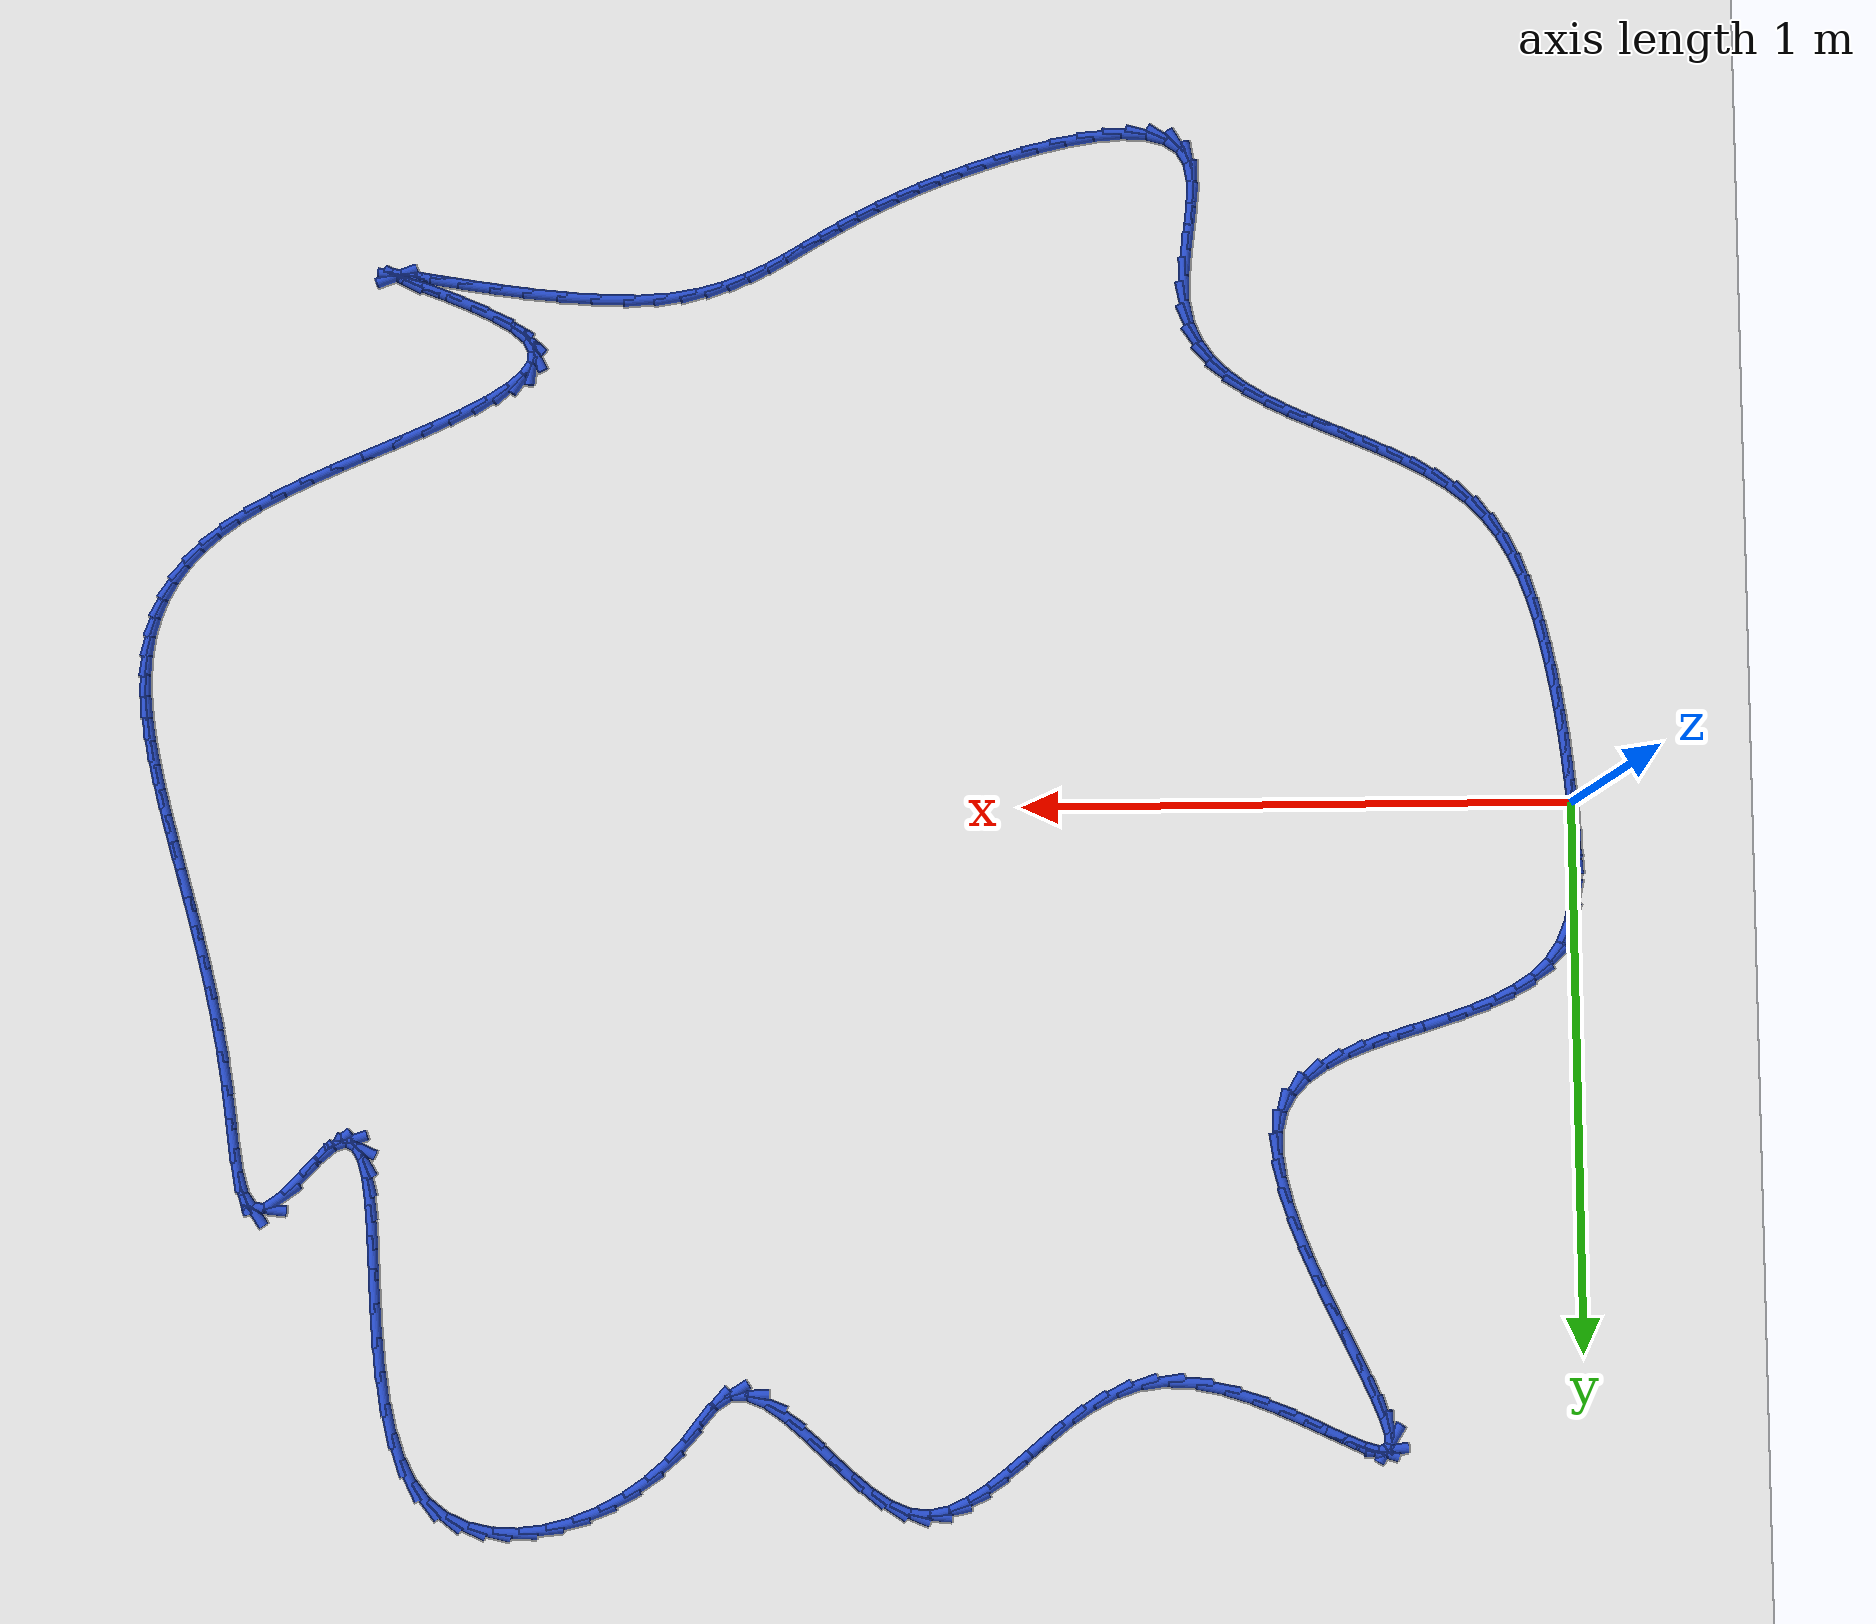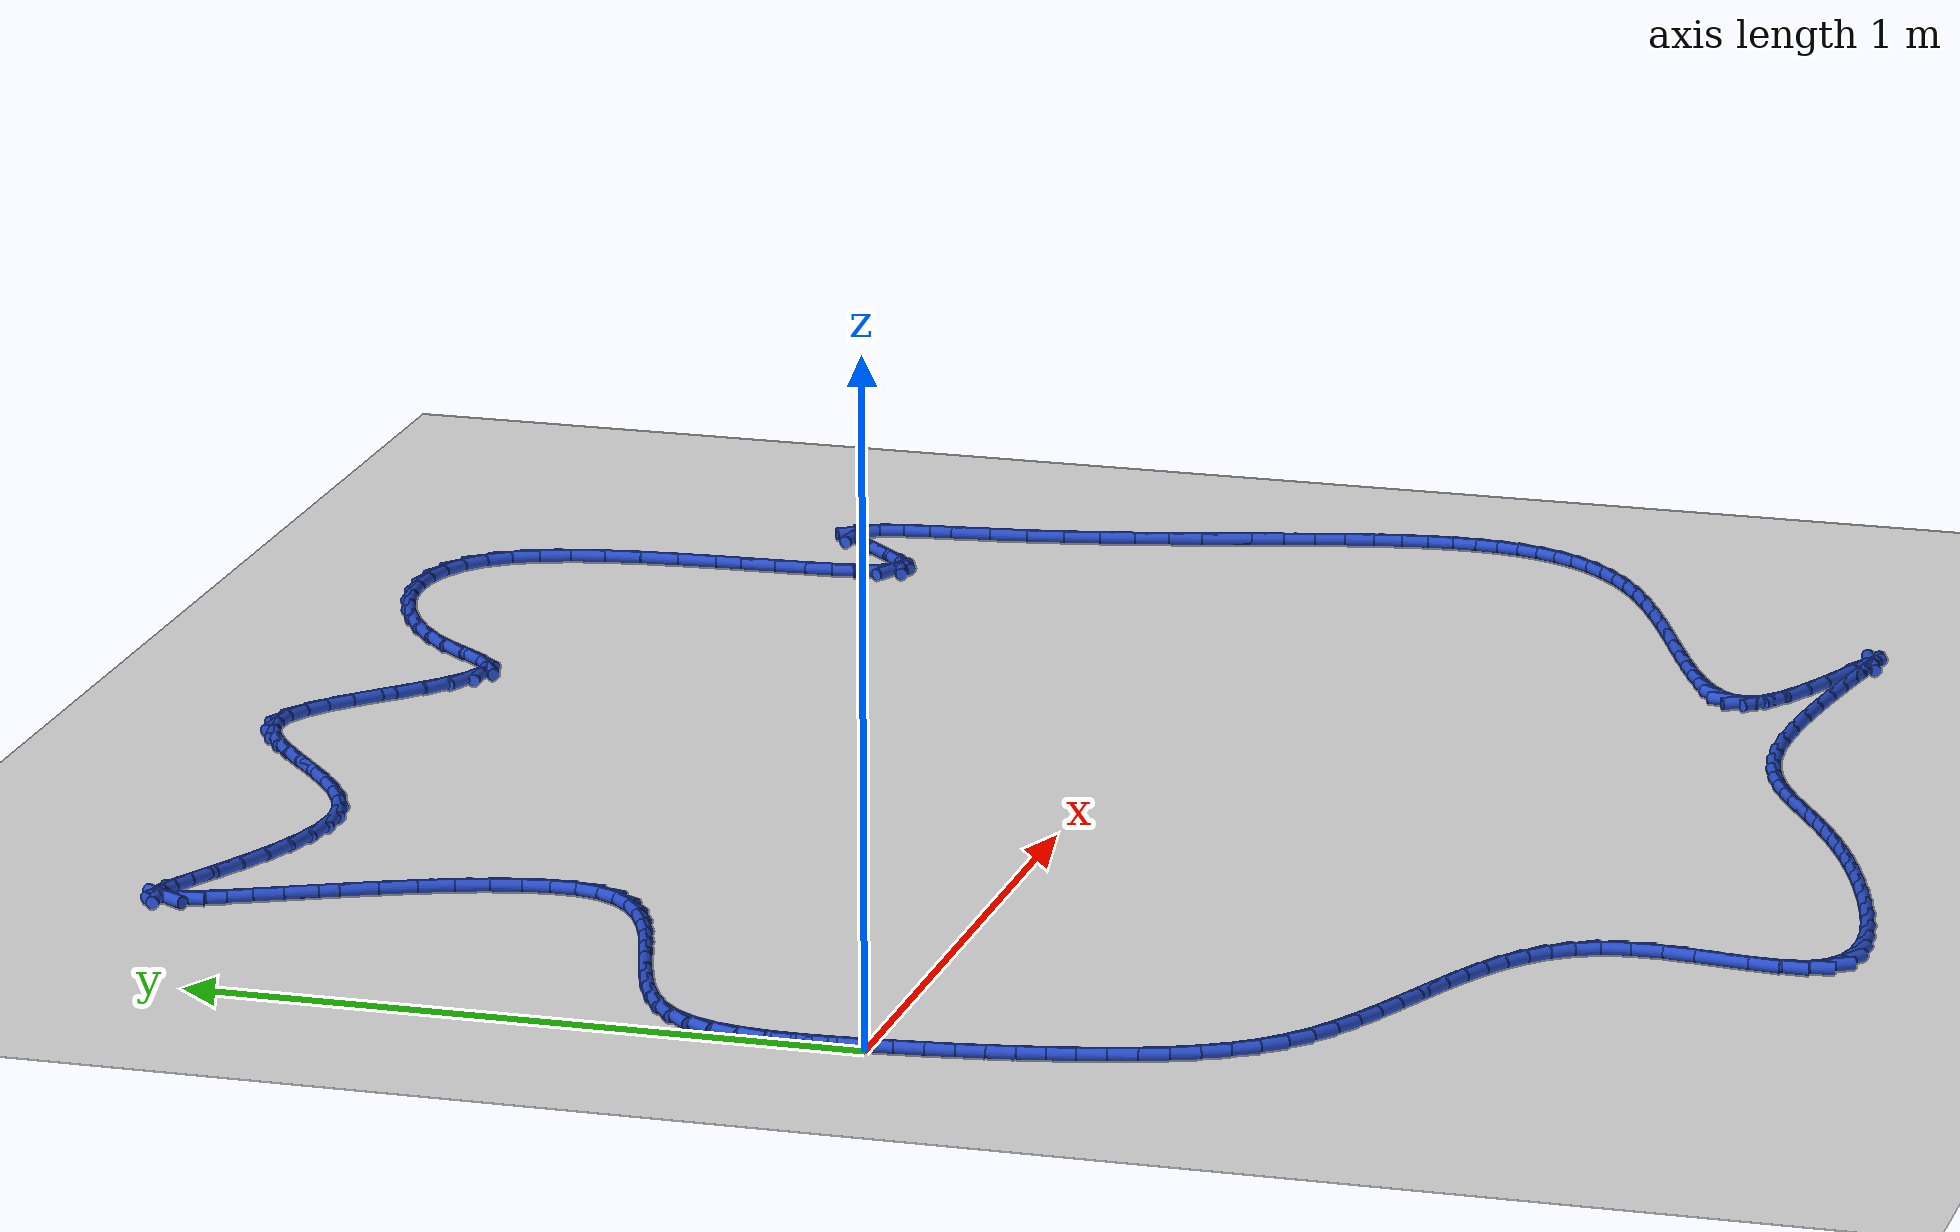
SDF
<sdf version="1.6">
 <world name="default">
  <light name="sun" type="directional">
   <pose>0 0 10 0 -0 0</pose>
   <diffuse>0.8 0.8 0.8 1</diffuse>
   <specular>0.2 0.2 0.2 1</specular>
   <attenuation>
    <range>1000</range>
    <constant>0.9</constant>
    <linear>0.01</linear>
    <quadratic>0.001</quadratic>
   </attenuation>
   <direction>-0.5 0.1 -0.9</direction>
  </light>
  <model name="ground_plane">
   <static>1</static>
   <link name="link">
    <collision name="collision">
     <geometry><plane><normal>0 0 1</normal><size>100 100</size></plane></geometry>
     <surface><friction><ode><mu>100</mu><mu2>50</mu2></ode></friction></surface>
    </collision>
    <visual name="visual">
     <cast_shadows>0</cast_shadows>
     <geometry><plane><normal>0 0 1</normal><size>100 100</size></plane></geometry>
     <material>
      <script><uri>file://media/materials/scripts/gazebo.material</uri><name>Gazebo/WhiteGlow</name></script>
     </material>
    </visual>
   </link>
  </model>
  <gravity>0 0 -9.8</gravity>
  <magnetic_field>6e-06 2.3e-05 -4.2e-05</magnetic_field>
  <atmosphere type="adiabatic"/>
  <physics name="default_physics" default="0" type="ode">
   <max_step_size>0.001</max_step_size>
   <real_time_factor>1</real_time_factor>
   <real_time_update_rate>1000</real_time_update_rate>
  </physics>
  <scene><ambient>0.4 0.4 0.4 1</ambient><background>0.7 0.7 0.7 1</background><shadows>1</shadows></scene>
  <spherical_coordinates>
   <surface_model>EARTH_WGS84</surface_model>
   <latitude_deg>0</latitude_deg>
   <longitude_deg>0</longitude_deg>
   <elevation>0</elevation>
   <heading_deg>0</heading_deg>
  </spherical_coordinates>
  <model name="line">
   <link name="link_0">
    <pose>2.6454533008646308e-17 -2.7755575615628914e-17 0.01 0 1.57 -1.5002465072789468</pose>
    <collision name="collision">
     <geometry><cylinder><radius>0.01</radius><length>0.08</length></cylinder></geometry>
    </collision>
    <visual name="visual">
     <material>
      <script><name>Gazebo/Blue</name><uri>file://media/materials/scripts/gazebo.material</uri></script>
     </material>
     <geometry><cylinder><radius>0.01</radius><length>0.08</length></cylinder></geometry>
    </visual>
   </link>
   <link name="link_1">
    <pose>-0.0031910155406945067 0.04515560231839195 0.01 0 1.57 -1.534526395487367</pose>
    <collision name="collision">
     <geometry><cylinder><radius>0.01</radius><length>0.08</length></cylinder></geometry>
    </collision>
    <visual name="visual">
     <material>
      <script><name>Gazebo/Blue</name><uri>file://media/materials/scripts/gazebo.material</uri></script>
     </material>
     <geometry><cylinder><radius>0.01</radius><length>0.08</length></cylinder></geometry>
    </visual>
   </link>
   <link name="link_2">
    <pose>-0.0048461995546252605 0.09077074654580536 0.01 0 1.57 1.5497232177446134</pose>
    <collision name="collision">
     <geometry><cylinder><radius>0.01</radius><length>0.08</length></cylinder></geometry>
    </collision>
    <visual name="visual">
     <material>
      <script><name>Gazebo/Blue</name><uri>file://media/materials/scripts/gazebo.material</uri></script>
     </material>
     <geometry><cylinder><radius>0.01</radius><length>0.08</length></cylinder></geometry>
    </visual>
   </link>
   <link name="link_3">
    <pose>-0.0038965086762597296 0.13583055683068881 0.01 0 1.57 1.4648789085244343</pose>
    <collision name="collision">
     <geometry><cylinder><radius>0.01</radius><length>0.08</length></cylinder></geometry>
    </collision>
    <visual name="visual">
     <material>
      <script><name>Gazebo/Blue</name><uri>file://media/materials/scripts/gazebo.material</uri></script>
     </material>
     <geometry><cylinder><radius>0.01</radius><length>0.08</length></cylinder></geometry>
    </visual>
   </link>
   <link name="link_4">
    <pose>0.0007271004599345848 0.17932015732149093 0.01 0 1.57 1.3456909850739898</pose>
    <collision name="collision">
     <geometry><cylinder><radius>0.01</radius><length>0.08</length></cylinder></geometry>
    </collision>
    <visual name="visual">
     <material>
      <script><name>Gazebo/Blue</name><uri>file://media/materials/scripts/gazebo.material</uri></script>
     </material>
     <geometry><cylinder><radius>0.01</radius><length>0.08</length></cylinder></geometry>
    </visual>
   </link>
   <link name="link_5">
    <pose>0.010093671219490197 0.2202246721666603 0.01 0 1.57 1.1843707430381305</pose>
    <collision name="collision">
     <geometry><cylinder><radius>0.01</radius><length>0.08</length></cylinder></geometry>
    </collision>
    <visual name="visual">
     <material>
      <script><name>Gazebo/Blue</name><uri>file://media/materials/scripts/gazebo.material</uri></script>
     </material>
     <geometry><cylinder><radius>0.01</radius><length>0.08</length></cylinder></geometry>
    </visual>
   </link>
   <link name="link_6">
    <pose>0.02527224696793958 0.2575292255146455 0.01 0 1.57 0.9774338475238803</pose>
    <collision name="collision">
     <geometry><cylinder><radius>0.01</radius><length>0.08</length></cylinder></geometry>
    </collision>
    <visual name="visual">
     <material>
      <script><name>Gazebo/Blue</name><uri>file://media/materials/scripts/gazebo.material</uri></script>
     </material>
     <geometry><cylinder><radius>0.01</radius><length>0.08</length></cylinder></geometry>
    </visual>
   </link>
   <link name="link_7">
    <pose>0.04732373669634079 0.2902253921291082 0.01 0 1.57 0.7587529641719621</pose>
    <collision name="collision">
     <geometry><cylinder><radius>0.01</radius><length>0.08</length></cylinder></geometry>
    </collision>
    <visual name="visual">
     <material>
      <script><name>Gazebo/Blue</name><uri>file://media/materials/scripts/gazebo.material</uri></script>
     </material>
     <geometry><cylinder><radius>0.01</radius><length>0.08</length></cylinder></geometry>
    </visual>
   </link>
   <link name="link_8">
    <pose>0.07653416477913576 0.31791923563353836 0.01 0 1.57 0.5862257848789586</pose>
    <collision name="collision">
     <geometry><cylinder><radius>0.01</radius><length>0.08</length></cylinder></geometry>
    </collision>
    <visual name="visual">
     <material>
      <script><name>Gazebo/Blue</name><uri>file://media/materials/scripts/gazebo.material</uri></script>
     </material>
     <geometry><cylinder><radius>0.01</radius><length>0.08</length></cylinder></geometry>
    </visual>
   </link>
   <link name="link_9">
    <pose>0.11178583341825085 0.34132998104192025 0.01 0 1.57 0.46266032682506864</pose>
    <collision name="collision">
     <geometry><cylinder><radius>0.01</radius><length>0.08</length></cylinder></geometry>
    </collision>
    <visual name="visual">
     <material>
      <script><name>Gazebo/Blue</name><uri>file://media/materials/scripts/gazebo.material</uri></script>
     </material>
     <geometry><cylinder><radius>0.01</radius><length>0.08</length></cylinder></geometry>
    </visual>
   </link>
   <link name="link_10">
    <pose>0.1518130486746015 0.36129421533155354 0.01 0 1.57 0.3793075172697864</pose>
    <collision name="collision">
     <geometry><cylinder><radius>0.01</radius><length>0.08</length></cylinder></geometry>
    </collision>
    <visual name="visual">
     <material>
      <script><name>Gazebo/Blue</name><uri>file://media/materials/scripts/gazebo.material</uri></script>
     </material>
     <geometry><cylinder><radius>0.01</radius><length>0.08</length></cylinder></geometry>
    </visual>
   </link>
   <link name="link_11">
    <pose>0.19535011660910287 0.3786485254797379 0.01 0 1.57 0.32803913888897657</pose>
    <collision name="collision">
     <geometry><cylinder><radius>0.01</radius><length>0.08</length></cylinder></geometry>
    </collision>
    <visual name="visual">
     <material>
      <script><name>Gazebo/Blue</name><uri>file://media/materials/scripts/gazebo.material</uri></script>
     </material>
     <geometry><cylinder><radius>0.01</radius><length>0.08</length></cylinder></geometry>
    </visual>
   </link>
   <link name="link_12">
    <pose>0.24113134328267055 0.3942294984637727 0.01 0 1.57 0.3035046907364256</pose>
    <collision name="collision">
     <geometry><cylinder><radius>0.01</radius><length>0.08</length></cylinder></geometry>
    </collision>
    <visual name="visual">
     <material>
      <script><name>Gazebo/Blue</name><uri>file://media/materials/scripts/gazebo.material</uri></script>
     </material>
     <geometry><cylinder><radius>0.01</radius><length>0.08</length></cylinder></geometry>
    </visual>
   </link>
   <link name="link_13">
    <pose>0.2878910347562199 0.40887372126095783 0.01 0 1.57 0.30330462855249307</pose>
    <collision name="collision">
     <geometry><cylinder><radius>0.01</radius><length>0.08</length></cylinder></geometry>
    </collision>
    <visual name="visual">
     <material>
      <script><name>Gazebo/Blue</name><uri>file://media/materials/scripts/gazebo.material</uri></script>
     </material>
     <geometry><cylinder><radius>0.01</radius><length>0.08</length></cylinder></geometry>
    </visual>
   </link>
   <link name="link_14">
    <pose>0.3343634970906661 0.42341778084859266 0.01 0 1.57 0.3278949474325294</pose>
    <collision name="collision">
     <geometry><cylinder><radius>0.01</radius><length>0.08</length></cylinder></geometry>
    </collision>
    <visual name="visual">
     <material>
      <script><name>Gazebo/Blue</name><uri>file://media/materials/scripts/gazebo.material</uri></script>
     </material>
     <geometry><cylinder><radius>0.01</radius><length>0.08</length></cylinder></geometry>
    </visual>
   </link>
   <link name="link_15">
    <pose>0.37928303634692473 0.4386982642039769 0.01 0 1.57 0.38077510317933083</pose>
    <collision name="collision">
     <geometry><cylinder><radius>0.01</radius><length>0.08</length></cylinder></geometry>
    </collision>
    <visual name="visual">
     <material>
      <script><name>Gazebo/Blue</name><uri>file://media/materials/scripts/gazebo.material</uri></script>
     </material>
     <geometry><cylinder><radius>0.01</radius><length>0.08</length></cylinder></geometry>
    </visual>
   </link>
   <link name="link_16">
    <pose>0.42138395858591116 0.45555175830441 0.01 0 1.57 0.46899479907376335</pose>
    <collision name="collision">
     <geometry><cylinder><radius>0.01</radius><length>0.08</length></cylinder></geometry>
    </collision>
    <visual name="visual">
     <material>
      <script><name>Gazebo/Blue</name><uri>file://media/materials/scripts/gazebo.material</uri></script>
     </material>
     <geometry><cylinder><radius>0.01</radius><length>0.08</length></cylinder></geometry>
    </visual>
   </link>
   <link name="link_17">
    <pose>0.45940056986854055 0.4748148501271916 0.01 0 1.57 0.6033463983947079</pose>
    <collision name="collision">
     <geometry><cylinder><radius>0.01</radius><length>0.08</length></cylinder></geometry>
    </collision>
    <visual name="visual">
     <material>
      <script><name>Gazebo/Blue</name><uri>file://media/materials/scripts/gazebo.material</uri></script>
     </material>
     <geometry><cylinder><radius>0.01</radius><length>0.08</length></cylinder></geometry>
    </visual>
   </link>
   <link name="link_18">
    <pose>0.4920671762557285 0.49732412664962145 0.01 0 1.57 0.7956772516427784</pose>
    <collision name="collision">
     <geometry><cylinder><radius>0.01</radius><length>0.08</length></cylinder></geometry>
    </collision>
    <visual name="visual">
     <material>
      <script><name>Gazebo/Blue</name><uri>file://media/materials/scripts/gazebo.material</uri></script>
     </material>
     <geometry><cylinder><radius>0.01</radius><length>0.08</length></cylinder></geometry>
    </visual>
   </link>
   <link name="link_19">
    <pose>0.5181180838083903 0.5239161748489991 0.01 0 1.57 1.0477595407057718</pose>
    <collision name="collision">
     <geometry><cylinder><radius>0.01</radius><length>0.08</length></cylinder></geometry>
    </collision>
    <visual name="visual">
     <material>
      <script><name>Gazebo/Blue</name><uri>file://media/materials/scripts/gazebo.material</uri></script>
     </material>
     <geometry><cylinder><radius>0.01</radius><length>0.08</length></cylinder></geometry>
    </visual>
   </link>
   <link name="link_20">
    <pose>0.5362875985874412 0.5554275817026241 0.01 0 1.57 1.3289871894173249</pose>
    <collision name="collision">
     <geometry><cylinder><radius>0.01</radius><length>0.08</length></cylinder></geometry>
    </collision>
    <visual name="visual">
     <material>
      <script><name>Gazebo/Blue</name><uri>file://media/materials/scripts/gazebo.material</uri></script>
     </material>
     <geometry><cylinder><radius>0.01</radius><length>0.08</length></cylinder></geometry>
    </visual>
   </link>
   <link name="link_21">
    <pose>0.5454525833274843 0.592587690681832 0.01 0 1.57 1.557955426080886</pose>
    <collision name="collision">
     <geometry><cylinder><radius>0.01</radius><length>0.08</length></cylinder></geometry>
    </collision>
    <visual name="visual">
     <material>
      <script><name>Gazebo/Blue</name><uri>file://media/materials/scripts/gazebo.material</uri></script>
     </material>
     <geometry><cylinder><radius>0.01</radius><length>0.08</length></cylinder></geometry>
    </visual>
   </link>
   <link name="link_22">
    <pose>0.5459971225542201 0.6349919821776754 0.01 0 1.57 -1.426071719680518</pose>
    <collision name="collision">
     <geometry><cylinder><radius>0.01</radius><length>0.08</length></cylinder></geometry>
    </collision>
    <visual name="visual">
     <material>
      <script><name>Gazebo/Blue</name><uri>file://media/materials/scripts/gazebo.material</uri></script>
     </material>
     <geometry><cylinder><radius>0.01</radius><length>0.08</length></cylinder></geometry>
    </visual>
   </link>
   <link name="link_23">
    <pose>0.5392109118573635 0.6815546573184943 0.01 0 1.57 -1.3180870062495131</pose>
    <collision name="collision">
     <geometry><cylinder><radius>0.01</radius><length>0.08</length></cylinder></geometry>
    </collision>
    <visual name="visual">
     <material>
      <script><name>Gazebo/Blue</name><uri>file://media/materials/scripts/gazebo.material</uri></script>
     </material>
     <geometry><cylinder><radius>0.01</radius><length>0.08</length></cylinder></geometry>
    </visual>
   </link>
   <link name="link_24">
    <pose>0.5263960046674354 0.7311806205919325 0.01 0 1.57 -1.2430658597152402</pose>
    <collision name="collision">
     <geometry><cylinder><radius>0.01</radius><length>0.08</length></cylinder></geometry>
    </collision>
    <visual name="visual">
     <material>
      <script><name>Gazebo/Blue</name><uri>file://media/materials/scripts/gazebo.material</uri></script>
     </material>
     <geometry><cylinder><radius>0.01</radius><length>0.08</length></cylinder></geometry>
    </visual>
   </link>
   <link name="link_25">
    <pose>0.5088544544149562 0.7827747764856342 0.01 0 1.57 -1.190631117307065</pose>
    <collision name="collision">
     <geometry><cylinder><radius>0.01</radius><length>0.08</length></cylinder></geometry>
    </collision>
    <visual name="visual">
     <material>
      <script><name>Gazebo/Blue</name><uri>file://media/materials/scripts/gazebo.material</uri></script>
     </material>
     <geometry><cylinder><radius>0.01</radius><length>0.08</length></cylinder></geometry>
    </visual>
   </link>
   <link name="link_26">
    <pose>0.4878883145304467 0.8352420294872428 0.01 0 1.57 -1.1546747554538452</pose>
    <collision name="collision">
     <geometry><cylinder><radius>0.01</radius><length>0.08</length></cylinder></geometry>
    </collision>
    <visual name="visual">
     <material>
      <script><name>Gazebo/Blue</name><uri>file://media/materials/scripts/gazebo.material</uri></script>
     </material>
     <geometry><cylinder><radius>0.01</radius><length>0.08</length></cylinder></geometry>
    </visual>
   </link>
   <link name="link_27">
    <pose>0.46479963844442757 0.8874872840844025 0.01 0 1.57 -1.1318709974345722</pose>
    <collision name="collision">
     <geometry><cylinder><radius>0.01</radius><length>0.08</length></cylinder></geometry>
    </collision>
    <visual name="visual">
     <material>
      <script><name>Gazebo/Blue</name><uri>file://media/materials/scripts/gazebo.material</uri></script>
     </material>
     <geometry><cylinder><radius>0.01</radius><length>0.08</length></cylinder></geometry>
    </visual>
   </link>
   <link name="link_28">
    <pose>0.44089047958741934 0.9384154447647566 0.01 0 1.57 -1.120935004586218</pose>
    <collision name="collision">
     <geometry><cylinder><radius>0.01</radius><length>0.08</length></cylinder></geometry>
    </collision>
    <visual name="visual">
     <material>
      <script><name>Gazebo/Blue</name><uri>file://media/materials/scripts/gazebo.material</uri></script>
     </material>
     <geometry><cylinder><radius>0.01</radius><length>0.08</length></cylinder></geometry>
    </visual>
   </link>
   <link name="link_29">
    <pose>0.41746289138994264 0.9869314160159498 0.01 0 1.57 -1.1225580075919648</pose>
    <collision name="collision">
     <geometry><cylinder><radius>0.01</radius><length>0.08</length></cylinder></geometry>
    </collision>
    <visual name="visual">
     <material>
      <script><name>Gazebo/Blue</name><uri>file://media/materials/scripts/gazebo.material</uri></script>
     </material>
     <geometry><cylinder><radius>0.01</radius><length>0.08</length></cylinder></geometry>
    </visual>
   </link>
   <link name="link_30">
    <pose>0.39581892728251833 1.0319401023256258 0.01 0 1.57 -1.1402422260604606</pose>
    <collision name="collision">
     <geometry><cylinder><radius>0.01</radius><length>0.08</length></cylinder></geometry>
    </collision>
    <visual name="visual">
     <material>
      <script><name>Gazebo/Blue</name><uri>file://media/materials/scripts/gazebo.material</uri></script>
     </material>
     <geometry><cylinder><radius>0.01</radius><length>0.08</length></cylinder></geometry>
    </visual>
   </link>
   <link name="link_31">
    <pose>0.377260640695667 1.0723464081814282 0.01 0 1.57 -1.1831814850915932</pose>
    <collision name="collision">
     <geometry><cylinder><radius>0.01</radius><length>0.08</length></cylinder></geometry>
    </collision>
    <visual name="visual">
     <material>
      <script><name>Gazebo/Blue</name><uri>file://media/materials/scripts/gazebo.material</uri></script>
     </material>
     <geometry><cylinder><radius>0.01</radius><length>0.08</length></cylinder></geometry>
    </visual>
   </link>
   <link name="link_32">
    <pose>0.36309008505990914 1.107055238071001 0.01 0 1.57 -1.2758631172956232</pose>
    <collision name="collision">
     <geometry><cylinder><radius>0.01</radius><length>0.08</length></cylinder></geometry>
    </collision>
    <visual name="visual">
     <material>
      <script><name>Gazebo/Blue</name><uri>file://media/materials/scripts/gazebo.material</uri></script>
     </material>
     <geometry><cylinder><radius>0.01</radius><length>0.08</length></cylinder></geometry>
    </visual>
   </link>
   <link name="link_33">
    <pose>0.35460931380576555 1.1349714964819877 0.01 0 1.57 -1.4965924245219366</pose>
    <collision name="collision">
     <geometry><cylinder><radius>0.01</radius><length>0.08</length></cylinder></geometry>
    </collision>
    <visual name="visual">
     <material>
      <script><name>Gazebo/Blue</name><uri>file://media/materials/scripts/gazebo.material</uri></script>
     </material>
     <geometry><cylinder><radius>0.01</radius><length>0.08</length></cylinder></geometry>
    </visual>
   </link>
   <link name="link_34">
    <pose>0.3531203803637569 1.1550000879020332 0.01 0 1.57 1.0186473919348549</pose>
    <collision name="collision">
     <geometry><cylinder><radius>0.01</radius><length>0.08</length></cylinder></geometry>
    </collision>
    <visual name="visual">
     <material>
      <script><name>Gazebo/Blue</name><uri>file://media/materials/scripts/gazebo.material</uri></script>
     </material>
     <geometry><cylinder><radius>0.01</radius><length>0.08</length></cylinder></geometry>
    </visual>
   </link>
   <link name="link_35">
    <pose>0.3599253381644037 1.16604591681878 0.01 0 1.57 0.0826007295407529</pose>
    <collision name="collision">
     <geometry><cylinder><radius>0.01</radius><length>0.08</length></cylinder></geometry>
    </collision>
    <visual name="visual">
     <material>
      <script><name>Gazebo/Blue</name><uri>file://media/materials/scripts/gazebo.material</uri></script>
     </material>
     <geometry><cylinder><radius>0.01</radius><length>0.08</length></cylinder></geometry>
    </visual>
   </link>
   <link name="link_36">
    <pose>0.3760257774485329 1.1673788577282314 0.01 0 1.57 -0.27894535806048254</pose>
    <collision name="collision">
     <geometry><cylinder><radius>0.01</radius><length>0.08</length></cylinder></geometry>
    </collision>
    <visual name="visual">
     <material>
      <script><name>Gazebo/Blue</name><uri>file://media/materials/scripts/gazebo.material</uri></script>
     </material>
     <geometry><cylinder><radius>0.01</radius><length>0.08</length></cylinder></geometry>
    </visual>
   </link>
   <link name="link_37">
    <pose>0.4007540835262429 1.1602963537551454 0.01 0 1.57 -0.3979805170856451</pose>
    <collision name="collision">
     <geometry><cylinder><radius>0.01</radius><length>0.08</length></cylinder></geometry>
    </collision>
    <visual name="visual">
     <material>
      <script><name>Gazebo/Blue</name><uri>file://media/materials/scripts/gazebo.material</uri></script>
     </material>
     <geometry><cylinder><radius>0.01</radius><length>0.08</length></cylinder></geometry>
    </visual>
   </link>
   <link name="link_38">
    <pose>0.4328663272996263 1.1467958920946417 0.01 0 1.57 -0.4381175252749171</pose>
    <collision name="collision">
     <geometry><cylinder><radius>0.01</radius><length>0.08</length></cylinder></geometry>
    </collision>
    <visual name="visual">
     <material>
      <script><name>Gazebo/Blue</name><uri>file://media/materials/scripts/gazebo.material</uri></script>
     </material>
     <geometry><cylinder><radius>0.01</radius><length>0.08</length></cylinder></geometry>
    </visual>
   </link>
   <link name="link_39">
    <pose>0.47111803375823735 1.1288756230570263 0.01 0 1.57 -0.44055578273512447</pose>
    <collision name="collision">
     <geometry><cylinder><radius>0.01</radius><length>0.08</length></cylinder></geometry>
    </collision>
    <visual name="visual">
     <material>
      <script><name>Gazebo/Blue</name><uri>file://media/materials/scripts/gazebo.material</uri></script>
     </material>
     <geometry><cylinder><radius>0.01</radius><length>0.08</length></cylinder></geometry>
    </visual>
   </link>
   <link name="link_40">
    <pose>0.5142647278916297 1.1085336969526027 0.01 0 1.57 -0.41762950680833794</pose>
    <collision name="collision">
     <geometry><cylinder><radius>0.01</radius><length>0.08</length></cylinder></geometry>
    </collision>
    <visual name="visual">
     <material>
      <script><name>Gazebo/Blue</name><uri>file://media/materials/scripts/gazebo.material</uri></script>
     </material>
     <geometry><cylinder><radius>0.01</radius><length>0.08</length></cylinder></geometry>
    </visual>
   </link>
   <link name="link_41">
    <pose>0.561061934689358 1.087768264091677 0.01 0 1.57 -0.37188295749838635</pose>
    <collision name="collision">
     <geometry><cylinder><radius>0.01</radius><length>0.08</length></cylinder></geometry>
    </collision>
    <visual name="visual">
     <material>
      <script><name>Gazebo/Blue</name><uri>file://media/materials/scripts/gazebo.material</uri></script>
     </material>
     <geometry><cylinder><radius>0.01</radius><length>0.08</length></cylinder></geometry>
    </visual>
   </link>
   <link name="link_42">
    <pose>0.6102651791409763 1.0685774747845533 0.01 0 1.57 -0.30069452287116466</pose>
    <collision name="collision">
     <geometry><cylinder><radius>0.01</radius><length>0.08</length></cylinder></geometry>
    </collision>
    <visual name="visual">
     <material>
      <script><name>Gazebo/Blue</name><uri>file://media/materials/scripts/gazebo.material</uri></script>
     </material>
     <geometry><cylinder><radius>0.01</radius><length>0.08</length></cylinder></geometry>
    </visual>
   </link>
   <link name="link_43">
    <pose>0.6606299862360386 1.052959479341537 0.01 0 1.57 -0.1972171807309845</pose>
    <collision name="collision">
     <geometry><cylinder><radius>0.01</radius><length>0.08</length></cylinder></geometry>
    </collision>
    <visual name="visual">
     <material>
      <script><name>Gazebo/Blue</name><uri>file://media/materials/scripts/gazebo.material</uri></script>
     </material>
     <geometry><cylinder><radius>0.01</radius><length>0.08</length></cylinder></geometry>
    </visual>
   </link>
   <link name="link_44">
    <pose>0.7109118809640993 1.0429124280729325 0.01 0 1.57 -0.05057437768826072</pose>
    <collision name="collision">
     <geometry><cylinder><radius>0.01</radius><length>0.08</length></cylinder></geometry>
    </collision>
    <visual name="visual">
     <material>
      <script><name>Gazebo/Blue</name><uri>file://media/materials/scripts/gazebo.material</uri></script>
     </material>
     <geometry><cylinder><radius>0.01</radius><length>0.08</length></cylinder></geometry>
    </visual>
   </link>
   <link name="link_45">
    <pose>0.7598663883147128 1.0404344712890456 0.01 0 1.57 0.14530475534830586</pose>
    <collision name="collision">
     <geometry><cylinder><radius>0.01</radius><length>0.08</length></cylinder></geometry>
    </collision>
    <visual name="visual">
     <material>
      <script><name>Gazebo/Blue</name><uri>file://media/materials/scripts/gazebo.material</uri></script>
     </material>
     <geometry><cylinder><radius>0.01</radius><length>0.08</length></cylinder></geometry>
    </visual>
   </link>
   <link name="link_46">
    <pose>0.8063640251267281 1.047238753914048 0.01 0 1.57 0.3374678605947326</pose>
    <collision name="collision">
     <geometry><cylinder><radius>0.01</radius><length>0.08</length></cylinder></geometry>
    </collision>
    <visual name="visual">
     <material>
      <script><name>Gazebo/Blue</name><uri>file://media/materials/scripts/gazebo.material</uri></script>
     </material>
     <geometry><cylinder><radius>0.01</radius><length>0.08</length></cylinder></geometry>
    </visual>
   </link>
   <link name="link_47">
    <pose>0.8502446068547291 1.062636030372734 0.01 0 1.57 0.4883731171705176</pose>
    <collision name="collision">
     <geometry><cylinder><radius>0.01</radius><length>0.08</length></cylinder></geometry>
    </collision>
    <visual name="visual">
     <material>
      <script><name>Gazebo/Blue</name><uri>file://media/materials/scripts/gazebo.material</uri></script>
     </material>
     <geometry><cylinder><radius>0.01</radius><length>0.08</length></cylinder></geometry>
    </visual>
   </link>
   <link name="link_48">
    <pose>0.8918339672789984 1.0847324667522746 0.01 0 1.57 0.5962434858115848</pose>
    <collision name="collision">
     <geometry><cylinder><radius>0.01</radius><length>0.08</length></cylinder></geometry>
    </collision>
    <visual name="visual">
     <material>
      <script><name>Gazebo/Blue</name><uri>file://media/materials/scripts/gazebo.material</uri></script>
     </material>
     <geometry><cylinder><radius>0.01</radius><length>0.08</length></cylinder></geometry>
    </visual>
   </link>
   <link name="link_49">
    <pose>0.9314615828141208 1.1116252009313001 0.01 0 1.57 0.6648728457711238</pose>
    <collision name="collision">
     <geometry><cylinder><radius>0.01</radius><length>0.08</length></cylinder></geometry>
    </collision>
    <visual name="visual">
     <material>
      <script><name>Gazebo/Blue</name><uri>file://media/materials/scripts/gazebo.material</uri></script>
     </material>
     <geometry><cylinder><radius>0.01</radius><length>0.08</length></cylinder></geometry>
    </visual>
   </link>
   <link name="link_50">
    <pose>0.9694569298746816 1.141411370788442 0.01 0 1.57 0.6979402985430583</pose>
    <collision name="collision">
     <geometry><cylinder><radius>0.01</radius><length>0.08</length></cylinder></geometry>
    </collision>
    <visual name="visual">
     <material>
      <script><name>Gazebo/Blue</name><uri>file://media/materials/scripts/gazebo.material</uri></script>
     </material>
     <geometry><cylinder><radius>0.01</radius><length>0.08</length></cylinder></geometry>
    </visual>
   </link>
   <link name="link_51">
    <pose>1.0061494848752657 1.17218811420233 0.01 0 1.57 0.6963622326337171</pose>
    <collision name="collision">
     <geometry><cylinder><radius>0.01</radius><length>0.08</length></cylinder></geometry>
    </collision>
    <visual name="visual">
     <material>
      <script><name>Gazebo/Blue</name><uri>file://media/materials/scripts/gazebo.material</uri></script>
     </material>
     <geometry><cylinder><radius>0.01</radius><length>0.08</length></cylinder></geometry>
    </visual>
   </link>
   <link name="link_52">
    <pose>1.0418687242304585 1.2020525690515962 0.01 0 1.57 0.6569165279694982</pose>
    <collision name="collision">
     <geometry><cylinder><radius>0.01</radius><length>0.08</length></cylinder></geometry>
    </collision>
    <visual name="visual">
     <material>
      <script><name>Gazebo/Blue</name><uri>file://media/materials/scripts/gazebo.material</uri></script>
     </material>
     <geometry><cylinder><radius>0.01</radius><length>0.08</length></cylinder></geometry>
    </visual>
   </link>
   <link name="link_53">
    <pose>1.0769441243548448 1.2291018732148702 0.01 0 1.57 0.571030258077261</pose>
    <collision name="collision">
     <geometry><cylinder><radius>0.01</radius><length>0.08</length></cylinder></geometry>
    </collision>
    <visual name="visual">
     <material>
      <script><name>Gazebo/Blue</name><uri>file://media/materials/scripts/gazebo.material</uri></script>
     </material>
     <geometry><cylinder><radius>0.01</radius><length>0.08</length></cylinder></geometry>
    </visual>
   </link>
   <link name="link_54">
    <pose>1.1117051616630098 1.251433164570783 0.01 0 1.57 0.4243152058732019</pose>
    <collision name="collision">
     <geometry><cylinder><radius>0.01</radius><length>0.08</length></cylinder></geometry>
    </collision>
    <visual name="visual">
     <material>
      <script><name>Gazebo/Blue</name><uri>file://media/materials/scripts/gazebo.material</uri></script>
     </material>
     <geometry><cylinder><radius>0.01</radius><length>0.08</length></cylinder></geometry>
    </visual>
   </link>
   <link name="link_55">
    <pose>1.146481312569539 1.2671435809979656 0.01 0 1.57 0.20184136599219352</pose>
    <collision name="collision">
     <geometry><cylinder><radius>0.01</radius><length>0.08</length></cylinder></geometry>
    </collision>
    <visual name="visual">
     <material>
      <script><name>Gazebo/Blue</name><uri>file://media/materials/scripts/gazebo.material</uri></script>
     </material>
     <geometry><cylinder><radius>0.01</radius><length>0.08</length></cylinder></geometry>
    </visual>
   </link>
   <link name="link_56">
    <pose>1.1816020534890168 1.2743302603750486 0.01 0 1.57 -0.09026770496880204</pose>
    <collision name="collision">
     <geometry><cylinder><radius>0.01</radius><length>0.08</length></cylinder></geometry>
    </collision>
    <visual name="visual">
     <material>
      <script><name>Gazebo/Blue</name><uri>file://media/materials/scripts/gazebo.material</uri></script>
     </material>
     <geometry><cylinder><radius>0.01</radius><length>0.08</length></cylinder></geometry>
    </visual>
   </link>
   <link name="link_57">
    <pose>1.217396860836029 1.2710903405806628 0.01 0 1.57 -0.3928688101757151</pose>
    <collision name="collision">
     <geometry><cylinder><radius>0.01</radius><length>0.08</length></cylinder></geometry>
    </collision>
    <visual name="visual">
     <material>
      <script><name>Gazebo/Blue</name><uri>file://media/materials/scripts/gazebo.material</uri></script>
     </material>
     <geometry><cylinder><radius>0.01</radius><length>0.08</length></cylinder></geometry>
    </visual>
   </link>
   <link name="link_58">
    <pose>1.2541467717845567 1.2558607208425892 0.01 0 1.57 -0.5974404741642019</pose>
    <collision name="collision">
     <geometry><cylinder><radius>0.01</radius><length>0.08</length></cylinder></geometry>
    </collision>
    <visual name="visual">
     <material>
      <script><name>Gazebo/Blue</name><uri>file://media/materials/scripts/gazebo.material</uri></script>
     </material>
     <geometry><cylinder><radius>0.01</radius><length>0.08</length></cylinder></geometry>
    </visual>
   </link>
   <link name="link_59">
    <pose>1.291669081027029 1.2303310716795635 0.01 0 1.57 -0.7068672895988576</pose>
    <collision name="collision">
     <geometry><cylinder><radius>0.01</radius><length>0.08</length></cylinder></geometry>
    </collision>
    <visual name="visual">
     <material>
      <script><name>Gazebo/Blue</name><uri>file://media/materials/scripts/gazebo.material</uri></script>
     </material>
     <geometry><cylinder><radius>0.01</radius><length>0.08</length></cylinder></geometry>
    </visual>
   </link>
   <link name="link_60">
    <pose>1.329523181777575 1.1980000299178448 0.01 0 1.57 -0.7563951312689297</pose>
    <collision name="collision">
     <geometry><cylinder><radius>0.01</radius><length>0.08</length></cylinder></geometry>
    </collision>
    <visual name="visual">
     <material>
      <script><name>Gazebo/Blue</name><uri>file://media/materials/scripts/gazebo.material</uri></script>
     </material>
     <geometry><cylinder><radius>0.01</radius><length>0.08</length></cylinder></geometry>
    </visual>
   </link>
   <link name="link_61">
    <pose>1.367265693791644 1.162385685910472 0.01 0 1.57 -0.7604886217314138</pose>
    <collision name="collision">
     <geometry><cylinder><radius>0.01</radius><length>0.08</length></cylinder></geometry>
    </collision>
    <visual name="visual">
     <material>
      <script><name>Gazebo/Blue</name><uri>file://media/materials/scripts/gazebo.material</uri></script>
     </material>
     <geometry><cylinder><radius>0.01</radius><length>0.08</length></cylinder></geometry>
    </visual>
   </link>
   <link name="link_62">
    <pose>1.4044532368246825 1.127006130010484 0.01 0 1.57 -0.7182213933987966</pose>
    <collision name="collision">
     <geometry><cylinder><radius>0.01</radius><length>0.08</length></cylinder></geometry>
    </collision>
    <visual name="visual">
     <material>
      <script><name>Gazebo/Blue</name><uri>file://media/materials/scripts/gazebo.material</uri></script>
     </material>
     <geometry><cylinder><radius>0.01</radius><length>0.08</length></cylinder></geometry>
    </visual>
   </link>
   <link name="link_63">
    <pose>1.4406424306321381 1.0953794525709195 0.01 0 1.57 -0.6113531034926124</pose>
    <collision name="collision">
     <geometry><cylinder><radius>0.01</radius><length>0.08</length></cylinder></geometry>
    </collision>
    <visual name="visual">
     <material>
      <script><name>Gazebo/Blue</name><uri>file://media/materials/scripts/gazebo.material</uri></script>
     </material>
     <geometry><cylinder><radius>0.01</radius><length>0.08</length></cylinder></geometry>
    </visual>
   </link>
   <link name="link_64">
    <pose>1.475389894969458 1.0710237439448176 0.01 0 1.57 -0.3915197334691016</pose>
    <collision name="collision">
     <geometry><cylinder><radius>0.01</radius><length>0.08</length></cylinder></geometry>
    </collision>
    <visual name="visual">
     <material>
      <script><name>Gazebo/Blue</name><uri>file://media/materials/scripts/gazebo.material</uri></script>
     </material>
     <geometry><cylinder><radius>0.01</radius><length>0.08</length></cylinder></geometry>
    </visual>
   </link>
   <link name="link_65">
    <pose>1.50825224959209 1.0574570944852166 0.01 0 1.57 0.02424701048360126</pose>
    <collision name="collision">
     <geometry><cylinder><radius>0.01</radius><length>0.08</length></cylinder></geometry>
    </collision>
    <visual name="visual">
     <material>
      <script><name>Gazebo/Blue</name><uri>file://media/materials/scripts/gazebo.material</uri></script>
     </material>
     <geometry><cylinder><radius>0.01</radius><length>0.08</length></cylinder></geometry>
    </visual>
   </link>
   <link name="link_66">
    <pose>1.5387861142554813 1.0581975945451552 0.01 0 1.57 0.567214867202811</pose>
    <collision name="collision">
     <geometry><cylinder><radius>0.01</radius><length>0.08</length></cylinder></geometry>
    </collision>
    <visual name="visual">
     <material>
      <script><name>Gazebo/Blue</name><uri>file://media/materials/scripts/gazebo.material</uri></script>
     </material>
     <geometry><cylinder><radius>0.01</radius><length>0.08</length></cylinder></geometry>
    </visual>
   </link>
   <link name="link_67">
    <pose>1.5667709042136324 1.076025197668674 0.01 0 1.57 0.853590785954401</pose>
    <collision name="collision">
     <geometry><cylinder><radius>0.01</radius><length>0.08</length></cylinder></geometry>
    </collision>
    <visual name="visual">
     <material>
      <script><name>Gazebo/Blue</name><uri>file://media/materials/scripts/gazebo.material</uri></script>
     </material>
     <geometry><cylinder><radius>0.01</radius><length>0.08</length></cylinder></geometry>
    </visual>
   </link>
   <link name="link_68">
    <pose>1.5939553986205288 1.1071952193603174 0.01 0 1.57 0.9081209353734886</pose>
    <collision name="collision">
     <geometry><cylinder><radius>0.01</radius><length>0.08</length></cylinder></geometry>
    </collision>
    <visual name="visual">
     <material>
      <script><name>Gazebo/Blue</name><uri>file://media/materials/scripts/gazebo.material</uri></script>
     </material>
     <geometry><cylinder><radius>0.01</radius><length>0.08</length></cylinder></geometry>
    </visual>
   </link>
   <link name="link_69">
    <pose>1.6231153425631857 1.1445605663610754 0.01 0 1.57 0.8265201986223273</pose>
    <collision name="collision">
     <geometry><cylinder><radius>0.01</radius><length>0.08</length></cylinder></geometry>
    </collision>
    <visual name="visual">
     <material>
      <script><name>Gazebo/Blue</name><uri>file://media/materials/scripts/gazebo.material</uri></script>
     </material>
     <geometry><cylinder><radius>0.01</radius><length>0.08</length></cylinder></geometry>
    </visual>
   </link>
   <link name="link_70">
    <pose>1.6568746074022889 1.1812171056814356 0.01 0 1.57 0.7003595160909006</pose>
    <collision name="collision">
     <geometry><cylinder><radius>0.01</radius><length>0.08</length></cylinder></geometry>
    </collision>
    <visual name="visual">
     <material>
      <script><name>Gazebo/Blue</name><uri>file://media/materials/scripts/gazebo.material</uri></script>
     </material>
     <geometry><cylinder><radius>0.01</radius><length>0.08</length></cylinder></geometry>
    </visual>
   </link>
   <link name="link_71">
    <pose>1.6956891644969552 1.213934017785807 0.01 0 1.57 0.5826060441259663</pose>
    <collision name="collision">
     <geometry><cylinder><radius>0.01</radius><length>0.08</length></cylinder></geometry>
    </collision>
    <visual name="visual">
     <material>
      <script><name>Gazebo/Blue</name><uri>file://media/materials/scripts/gazebo.material</uri></script>
     </material>
     <geometry><cylinder><radius>0.01</radius><length>0.08</length></cylinder></geometry>
    </visual>
   </link>
   <link name="link_72">
    <pose>1.7384598159783882 1.242115578873599 0.01 0 1.57 0.46909349959408997</pose>
    <collision name="collision">
     <geometry><cylinder><radius>0.01</radius><length>0.08</length></cylinder></geometry>
    </collision>
    <visual name="visual">
     <material>
      <script><name>Gazebo/Blue</name><uri>file://media/materials/scripts/gazebo.material</uri></script>
     </material>
     <geometry><cylinder><radius>0.01</radius><length>0.08</length></cylinder></geometry>
    </visual>
   </link>
   <link name="link_73">
    <pose>1.784053409353 1.2652235982315279 0.01 0 1.57 0.35440661868051127</pose>
    <collision name="collision">
     <geometry><cylinder><radius>0.01</radius><length>0.08</length></cylinder></geometry>
    </collision>
    <visual name="visual">
     <material>
      <script><name>Gazebo/Blue</name><uri>file://media/materials/scripts/gazebo.material</uri></script>
     </material>
     <geometry><cylinder><radius>0.01</radius><length>0.08</length></cylinder></geometry>
    </visual>
   </link>
   <link name="link_74">
    <pose>1.8313367921272046 1.282719885146312 0.01 0 1.57 0.23287029272252555</pose>
    <collision name="collision">
     <geometry><cylinder><radius>0.01</radius><length>0.08</length></cylinder></geometry>
    </collision>
    <visual name="visual">
     <material>
      <script><name>Gazebo/Blue</name><uri>file://media/materials/scripts/gazebo.material</uri></script>
     </material>
     <geometry><cylinder><radius>0.01</radius><length>0.08</length></cylinder></geometry>
    </visual>
   </link>
   <link name="link_75">
    <pose>1.8791768118074121 1.2940662489046675 0.01 0 1.57 0.09824184688303902</pose>
    <collision name="collision">
     <geometry><cylinder><radius>0.01</radius><length>0.08</length></cylinder></geometry>
    </collision>
    <visual name="visual">
     <material>
      <script><name>Gazebo/Blue</name><uri>file://media/materials/scripts/gazebo.material</uri></script>
     </material>
     <geometry><cylinder><radius>0.01</radius><length>0.08</length></cylinder></geometry>
    </visual>
   </link>
   <link name="link_76">
    <pose>1.9264403159000378 1.2987244987933122 0.01 0 1.57 -0.056314454259459926</pose>
    <collision name="collision">
     <geometry><cylinder><radius>0.01</radius><length>0.08</length></cylinder></geometry>
    </collision>
    <visual name="visual">
     <material>
      <script><name>Gazebo/Blue</name><uri>file://media/materials/scripts/gazebo.material</uri></script>
     </material>
     <geometry><cylinder><radius>0.01</radius><length>0.08</length></cylinder></geometry>
    </visual>
   </link>
   <link name="link_77">
    <pose>1.971994151911492 1.2961564440989635 0.01 0 1.57 -0.23735743251210276</pose>
    <collision name="collision">
     <geometry><cylinder><radius>0.01</radius><length>0.08</length></cylinder></geometry>
    </collision>
    <visual name="visual">
     <material>
      <script><name>Gazebo/Blue</name><uri>file://media/materials/scripts/gazebo.material</uri></script>
     </material>
     <geometry><cylinder><radius>0.01</radius><length>0.08</length></cylinder></geometry>
    </visual>
   </link>
   <link name="link_78">
    <pose>2.014705167348189 1.2858238941083382 0.01 0 1.57 -0.4484095660053678</pose>
    <collision name="collision">
     <geometry><cylinder><radius>0.01</radius><length>0.08</length></cylinder></geometry>
    </collision>
    <visual name="visual">
     <material>
      <script><name>Gazebo/Blue</name><uri>file://media/materials/scripts/gazebo.material</uri></script>
     </material>
     <geometry><cylinder><radius>0.01</radius><length>0.08</length></cylinder></geometry>
    </visual>
   </link>
   <link name="link_79">
    <pose>2.0534402097165394 1.2671886581081537 0.01 0 1.57 -0.6850878543346153</pose>
    <collision name="collision">
     <geometry><cylinder><radius>0.01</radius><length>0.08</length></cylinder></geometry>
    </collision>
    <visual name="visual">
     <material>
      <script><name>Gazebo/Blue</name><uri>file://media/materials/scripts/gazebo.material</uri></script>
     </material>
     <geometry><cylinder><radius>0.01</radius><length>0.08</length></cylinder></geometry>
    </visual>
   </link>
   <link name="link_80">
    <pose>2.0870661265229566 1.2397125453851263 0.01 0 1.57 -0.9303681591934165</pose>
    <collision name="collision">
     <geometry><cylinder><radius>0.01</radius><length>0.08</length></cylinder></geometry>
    </collision>
    <visual name="visual">
     <material>
      <script><name>Gazebo/Blue</name><uri>file://media/materials/scripts/gazebo.material</uri></script>
     </material>
     <geometry><cylinder><radius>0.01</radius><length>0.08</length></cylinder></geometry>
    </visual>
   </link>
   <link name="link_81">
    <pose>2.1144934545787817 1.202907692473142 0.01 0 1.57 -1.1359588045288331</pose>
    <collision name="collision">
     <geometry><cylinder><radius>0.01</radius><length>0.08</length></cylinder></geometry>
    </collision>
    <visual name="visual">
     <material>
      <script><name>Gazebo/Blue</name><uri>file://media/materials/scripts/gazebo.material</uri></script>
     </material>
     <geometry><cylinder><radius>0.01</radius><length>0.08</length></cylinder></geometry>
    </visual>
   </link>
   <link name="link_82">
    <pose>2.1356202367636983 1.1574237788828645 0.01 0 1.57 -1.279580886405102</pose>
    <collision name="collision">
     <geometry><cylinder><radius>0.01</radius><length>0.08</length></cylinder></geometry>
    </collision>
    <visual name="visual">
     <material>
      <script><name>Gazebo/Blue</name><uri>file://media/materials/scripts/gazebo.material</uri></script>
     </material>
     <geometry><cylinder><radius>0.01</radius><length>0.08</length></cylinder></geometry>
    </visual>
   </link>
   <link name="link_83">
    <pose>2.151322479361811 1.1050370345714857 0.01 0 1.57 -1.378384507369205</pose>
    <collision name="collision">
     <geometry><cylinder><radius>0.01</radius><length>0.08</length></cylinder></geometry>
    </collision>
    <visual name="visual">
     <material>
      <script><name>Gazebo/Blue</name><uri>file://media/materials/scripts/gazebo.material</uri></script>
     </material>
     <geometry><cylinder><radius>0.01</radius><length>0.08</length></cylinder></geometry>
    </visual>
   </link>
   <link name="link_84">
    <pose>2.162517969372948 1.0475718181723286 0.01 0 1.57 -1.4461720254096713</pose>
    <collision name="collision">
     <geometry><cylinder><radius>0.01</radius><length>0.08</length></cylinder></geometry>
    </collision>
    <visual name="visual">
     <material>
      <script><name>Gazebo/Blue</name><uri>file://media/materials/scripts/gazebo.material</uri></script>
     </material>
     <geometry><cylinder><radius>0.01</radius><length>0.08</length></cylinder></geometry>
    </visual>
   </link>
   <link name="link_85">
    <pose>2.1701244937969384 0.9868524883187135 0.01 0 1.57 -1.49155122507483</pose>
    <collision name="collision">
     <geometry><cylinder><radius>0.01</radius><length>0.08</length></cylinder></geometry>
    </collision>
    <visual name="visual">
     <material>
      <script><name>Gazebo/Blue</name><uri>file://media/materials/scripts/gazebo.material</uri></script>
     </material>
     <geometry><cylinder><radius>0.01</radius><length>0.08</length></cylinder></geometry>
    </visual>
   </link>
   <link name="link_86">
    <pose>2.1750598396336107 0.9247034036439634 0.01 0 1.57 -1.5193159687592288</pose>
    <collision name="collision">
     <geometry><cylinder><radius>0.01</radius><length>0.08</length></cylinder></geometry>
    </collision>
    <visual name="visual">
     <material>
      <script><name>Gazebo/Blue</name><uri>file://media/materials/scripts/gazebo.material</uri></script>
     </material>
     <geometry><cylinder><radius>0.01</radius><length>0.08</length></cylinder></geometry>
    </visual>
   </link>
   <link name="link_87">
    <pose>2.1782417938827954 0.8629489227813977 0.01 0 1.57 -1.5314057906063097</pose>
    <collision name="collision">
     <geometry><cylinder><radius>0.01</radius><length>0.08</length></cylinder></geometry>
    </collision>
    <visual name="visual">
     <material>
      <script><name>Gazebo/Blue</name><uri>file://media/materials/scripts/gazebo.material</uri></script>
     </material>
     <geometry><cylinder><radius>0.01</radius><length>0.08</length></cylinder></geometry>
    </visual>
   </link>
   <link name="link_88">
    <pose>2.180588143544319 0.80341340436434 0.01 0 1.57 -1.5270607466632569</pose>
    <collision name="collision">
     <geometry><cylinder><radius>0.01</radius><length>0.08</length></cylinder></geometry>
    </collision>
    <visual name="visual">
     <material>
      <script><name>Gazebo/Blue</name><uri>file://media/materials/scripts/gazebo.material</uri></script>
     </material>
     <geometry><cylinder><radius>0.01</radius><length>0.08</length></cylinder></geometry>
    </visual>
   </link>
   <link name="link_89">
    <pose>2.183016675618013 0.7479212070261109 0.01 0 1.57 -1.5018170769415522</pose>
    <collision name="collision">
     <geometry><cylinder><radius>0.01</radius><length>0.08</length></cylinder></geometry>
    </collision>
    <visual name="visual">
     <material>
      <script><name>Gazebo/Blue</name><uri>file://media/materials/scripts/gazebo.material</uri></script>
     </material>
     <geometry><cylinder><radius>0.01</radius><length>0.08</length></cylinder></geometry>
    </visual>
   </link>
   <link name="link_90">
    <pose>2.186445177103705 0.6982966894000328 0.01 0 1.57 -1.4439836818935416</pose>
    <collision name="collision">
     <geometry><cylinder><radius>0.01</radius><length>0.08</length></cylinder></geometry>
    </collision>
    <visual name="visual">
     <material>
      <script><name>Gazebo/Blue</name><uri>file://media/materials/scripts/gazebo.material</uri></script>
     </material>
     <geometry><cylinder><radius>0.01</radius><length>0.08</length></cylinder></geometry>
    </visual>
   </link>
   <link name="link_91">
    <pose>2.1917914350012246 0.6563642101194259 0.01 0 1.57 -1.3235606368990032</pose>
    <collision name="collision">
     <geometry><cylinder><radius>0.01</radius><length>0.08</length></cylinder></geometry>
    </collision>
    <visual name="visual">
     <material>
      <script><name>Gazebo/Blue</name><uri>file://media/materials/scripts/gazebo.material</uri></script>
     </material>
     <geometry><cylinder><radius>0.01</radius><length>0.08</length></cylinder></geometry>
    </visual>
   </link>
   <link name="link_92">
    <pose>2.1999732363103996 0.6239481278176131 0.01 0 1.57 -1.0555186480664742</pose>
    <collision name="collision">
     <geometry><cylinder><radius>0.01</radius><length>0.08</length></cylinder></geometry>
    </collision>
    <visual name="visual">
     <material>
      <script><name>Gazebo/Blue</name><uri>file://media/materials/scripts/gazebo.material</uri></script>
     </material>
     <geometry><cylinder><radius>0.01</radius><length>0.08</length></cylinder></geometry>
    </visual>
   </link>
   <link name="link_93">
    <pose>2.211908368031061 0.6028728011279153 0.01 0 1.57 -0.4445406824527559</pose>
    <collision name="collision">
     <geometry><cylinder><radius>0.01</radius><length>0.08</length></cylinder></geometry>
    </collision>
    <visual name="visual">
     <material>
      <script><name>Gazebo/Blue</name><uri>file://media/materials/scripts/gazebo.material</uri></script>
     </material>
     <geometry><cylinder><radius>0.01</radius><length>0.08</length></cylinder></geometry>
    </visual>
   </link>
   <link name="link_94">
    <pose>2.228514617163037 0.5949625886836545 0.01 0 1.57 0.30875493954053534</pose>
    <collision name="collision">
     <geometry><cylinder><radius>0.01</radius><length>0.08</length></cylinder></geometry>
    </collision>
    <visual name="visual">
     <material>
      <script><name>Gazebo/Blue</name><uri>file://media/materials/scripts/gazebo.material</uri></script>
     </material>
     <geometry><cylinder><radius>0.01</radius><length>0.08</length></cylinder></geometry>
    </visual>
   </link>
   <link name="link_95">
    <pose>2.250709770706156 0.6020418491181521 0.01 0 1.57 0.6886831384111753</pose>
    <collision name="collision">
     <geometry><cylinder><radius>0.01</radius><length>0.08</length></cylinder></geometry>
    </collision>
    <visual name="visual">
     <material>
      <script><name>Gazebo/Blue</name><uri>file://media/materials/scripts/gazebo.material</uri></script>
     </material>
     <geometry><cylinder><radius>0.01</radius><length>0.08</length></cylinder></geometry>
    </visual>
   </link>
   <link name="link_96">
    <pose>2.2792705045789683 0.6255508925223636 0.01 0 1.57 0.8035148044822694</pose>
    <collision name="collision">
     <geometry><cylinder><radius>0.01</radius><length>0.08</length></cylinder></geometry>
    </collision>
    <visual name="visual">
     <material>
      <script><name>Gazebo/Blue</name><uri>file://media/materials/scripts/gazebo.material</uri></script>
     </material>
     <geometry><cylinder><radius>0.01</radius><length>0.08</length></cylinder></geometry>
    </visual>
   </link>
   <link name="link_97">
    <pose>2.3123863883004456 0.6598889487779306 0.01 0 1.57 0.7824583699170268</pose>
    <collision name="collision">
     <geometry><cylinder><radius>0.01</radius><length>0.08</length></cylinder></geometry>
    </collision>
    <visual name="visual">
     <material>
      <script><name>Gazebo/Blue</name><uri>file://media/materials/scripts/gazebo.material</uri></script>
     </material>
     <geometry><cylinder><radius>0.01</radius><length>0.08</length></cylinder></geometry>
    </visual>
   </link>
   <link name="link_98">
    <pose>2.3459801321723583 0.6932857537038963 0.01 0 1.57 0.6001998598195208</pose>
    <collision name="collision">
     <geometry><cylinder><radius>0.01</radius><length>0.08</length></cylinder></geometry>
    </collision>
    <visual name="visual">
     <material>
      <script><name>Gazebo/Blue</name><uri>file://media/materials/scripts/gazebo.material</uri></script>
     </material>
     <geometry><cylinder><radius>0.01</radius><length>0.08</length></cylinder></geometry>
    </visual>
   </link>
   <link name="link_99">
    <pose>2.375897735664824 0.7137622665808971 0.01 0 1.57 -0.11928949473259208</pose>
    <collision name="collision">
     <geometry><cylinder><radius>0.01</radius><length>0.08</length></cylinder></geometry>
    </collision>
    <visual name="visual">
     <material>
      <script><name>Gazebo/Blue</name><uri>file://media/materials/scripts/gazebo.material</uri></script>
     </material>
     <geometry><cylinder><radius>0.01</radius><length>0.08</length></cylinder></geometry>
    </visual>
   </link>
   <link name="link_100">
    <pose>2.3985846872018737 0.711043041164706 0.01 0 1.57 -1.0079754484178423</pose>
    <collision name="collision">
     <geometry><cylinder><radius>0.01</radius><length>0.08</length></cylinder></geometry>
    </collision>
    <visual name="visual">
     <material>
      <script><name>Gazebo/Blue</name><uri>file://media/materials/scripts/gazebo.material</uri></script>
     </material>
     <geometry><cylinder><radius>0.01</radius><length>0.08</length></cylinder></geometry>
    </visual>
   </link>
   <link name="link_101">
    <pose>2.41440017236094 0.6859743588165482 0.01 0 1.57 -1.3180890703956356</pose>
    <collision name="collision">
     <geometry><cylinder><radius>0.01</radius><length>0.08</length></cylinder></geometry>
    </collision>
    <visual name="visual">
     <material>
      <script><name>Gazebo/Blue</name><uri>file://media/materials/scripts/gazebo.material</uri></script>
     </material>
     <geometry><cylinder><radius>0.01</radius><length>0.08</length></cylinder></geometry>
    </visual>
   </link>
   <link name="link_102">
    <pose>2.4252738647091086 0.643865426602919 0.01 0 1.57 -1.4256948526047082</pose>
    <collision name="collision">
     <geometry><cylinder><radius>0.01</radius><length>0.08</length></cylinder></geometry>
    </collision>
    <visual name="visual">
     <material>
      <script><name>Gazebo/Blue</name><uri>file://media/materials/scripts/gazebo.material</uri></script>
     </material>
     <geometry><cylinder><radius>0.01</radius><length>0.08</length></cylinder></geometry>
    </visual>
   </link>
   <link name="link_103">
    <pose>2.433139663139325 0.5900374588871049 0.01 0 1.57 -1.4584984318471812</pose>
    <collision name="collision">
     <geometry><cylinder><radius>0.01</radius><length>0.08</length></cylinder></geometry>
    </collision>
    <visual name="visual">
     <material>
      <script><name>Gazebo/Blue</name><uri>file://media/materials/scripts/gazebo.material</uri></script>
     </material>
     <geometry><cylinder><radius>0.01</radius><length>0.08</length></cylinder></geometry>
    </visual>
   </link>
   <link name="link_104">
    <pose>2.4399314665445373 0.5298116700323912 0.01 0 1.57 -1.4473710631324117</pose>
    <collision name="collision">
     <geometry><cylinder><radius>0.01</radius><length>0.08</length></cylinder></geometry>
    </collision>
    <visual name="visual">
     <material>
      <script><name>Gazebo/Blue</name><uri>file://media/materials/scripts/gazebo.material</uri></script>
     </material>
     <geometry><cylinder><radius>0.01</radius><length>0.08</length></cylinder></geometry>
    </visual>
   </link>
   <link name="link_105">
    <pose>2.447547036387631 0.46842343441487894 0.01 0 1.57 -1.4160826711322243</pose>
    <collision name="collision">
     <geometry><cylinder><radius>0.01</radius><length>0.08</length></cylinder></geometry>
    </collision>
    <visual name="visual">
     <material>
      <script><name>Gazebo/Blue</name><uri>file://media/materials/scripts/gazebo.material</uri></script>
     </material>
     <geometry><cylinder><radius>0.01</radius><length>0.08</length></cylinder></geometry>
    </visual>
   </link>
   <link name="link_106">
    <pose>2.456863894455181 0.40868467348117266 0.01 0 1.57 -1.387339604484556</pose>
    <collision name="collision">
     <geometry><cylinder><radius>0.01</radius><length>0.08</length></cylinder></geometry>
    </collision>
    <visual name="visual">
     <material>
      <script><name>Gazebo/Blue</name><uri>file://media/materials/scripts/gazebo.material</uri></script>
     </material>
     <geometry><cylinder><radius>0.01</radius><length>0.08</length></cylinder></geometry>
    </visual>
   </link>
   <link name="link_107">
    <pose>2.4676217113124004 0.3507044840968019 0.01 0 1.57 -1.3626932122731474</pose>
    <collision name="collision">
     <geometry><cylinder><radius>0.01</radius><length>0.08</length></cylinder></geometry>
    </collision>
    <visual name="visual">
     <material>
      <script><name>Gazebo/Blue</name><uri>file://media/materials/scripts/gazebo.material</uri></script>
     </material>
     <geometry><cylinder><radius>0.01</radius><length>0.08</length></cylinder></geometry>
    </visual>
   </link>
   <link name="link_108">
    <pose>2.479500409975703 0.29445004022865595 0.01 0 1.57 -1.3424600609305835</pose>
    <collision name="collision">
     <geometry><cylinder><radius>0.01</radius><length>0.08</length></cylinder></geometry>
    </collision>
    <visual name="visual">
     <material>
      <script><name>Gazebo/Blue</name><uri>file://media/materials/scripts/gazebo.material</uri></script>
     </material>
     <geometry><cylinder><radius>0.01</radius><length>0.08</length></cylinder></geometry>
    </visual>
   </link>
   <link name="link_109">
    <pose>2.492179913461503 0.239888515843627 0.01 0 1.57 -1.3269766715767117</pose>
    <collision name="collision">
     <geometry><cylinder><radius>0.01</radius><length>0.08</length></cylinder></geometry>
    </collision>
    <visual name="visual">
     <material>
      <script><name>Gazebo/Blue</name><uri>file://media/materials/scripts/gazebo.material</uri></script>
     </material>
     <geometry><cylinder><radius>0.01</radius><length>0.08</length></cylinder></geometry>
    </visual>
   </link>
   <link name="link_110">
    <pose>2.5053401447862167 0.18698708490860466 0.01 0 1.57 -1.3166182717474295</pose>
    <collision name="collision">
     <geometry><cylinder><radius>0.01</radius><length>0.08</length></cylinder></geometry>
    </collision>
    <visual name="visual">
     <material>
      <script><name>Gazebo/Blue</name><uri>file://media/materials/scripts/gazebo.material</uri></script>
     </material>
     <geometry><cylinder><radius>0.01</radius><length>0.08</length></cylinder></geometry>
    </visual>
   </link>
   <link name="link_111">
    <pose>2.5186610269662566 0.13571292139048088 0.01 0 1.57 -1.3118196293289563</pose>
    <collision name="collision">
     <geometry><cylinder><radius>0.01</radius><length>0.08</length></cylinder></geometry>
    </collision>
    <visual name="visual">
     <material>
      <script><name>Gazebo/Blue</name><uri>file://media/materials/scripts/gazebo.material</uri></script>
     </material>
     <geometry><cylinder><radius>0.01</radius><length>0.08</length></cylinder></geometry>
    </visual>
   </link>
   <link name="link_112">
    <pose>2.531822483018037 0.0860331992561459 0.01 0 1.57 -1.3130976611758904</pose>
    <collision name="collision">
     <geometry><cylinder><radius>0.01</radius><length>0.08</length></cylinder></geometry>
    </collision>
    <visual name="visual">
     <material>
      <script><name>Gazebo/Blue</name><uri>file://media/materials/scripts/gazebo.material</uri></script>
     </material>
     <geometry><cylinder><radius>0.01</radius><length>0.08</length></cylinder></geometry>
    </visual>
   </link>
   <link name="link_113">
    <pose>2.544504435957974 0.03791509247249044 0.01 0 1.57 -1.3210750861983023</pose>
    <collision name="collision">
     <geometry><cylinder><radius>0.01</radius><length>0.08</length></cylinder></geometry>
    </collision>
    <visual name="visual">
     <material>
      <script><name>Gazebo/Blue</name><uri>file://media/materials/scripts/gazebo.material</uri></script>
     </material>
     <geometry><cylinder><radius>0.01</radius><length>0.08</length></cylinder></geometry>
    </visual>
   </link>
   <link name="link_114">
    <pose>2.5563868088024804 -0.008674224993595842 0.01 0 1.57 -1.336503311395331</pose>
    <collision name="collision">
     <geometry><cylinder><radius>0.01</radius><length>0.08</length></cylinder></geometry>
    </collision>
    <visual name="visual">
     <material>
      <script><name>Gazebo/Blue</name><uri>file://media/materials/scripts/gazebo.material</uri></script>
     </material>
     <geometry><cylinder><radius>0.01</radius><length>0.08</length></cylinder></geometry>
    </visual>
   </link>
   <link name="link_115">
    <pose>2.5671495245679714 -0.053767579175219786 0.01 0 1.57 -1.3602805006787935</pose>
    <collision name="collision">
     <geometry><cylinder><radius>0.01</radius><length>0.08</length></cylinder></geometry>
    </collision>
    <visual name="visual">
     <material>
      <script><name>Gazebo/Blue</name><uri>file://media/materials/scripts/gazebo.material</uri></script>
     </material>
     <geometry><cylinder><radius>0.01</radius><length>0.08</length></cylinder></geometry>
    </visual>
   </link>
   <link name="link_116">
    <pose>2.576472506270861 -0.09739779610549178 0.01 0 1.57 -1.3934566347480566</pose>
    <collision name="collision">
     <geometry><cylinder><radius>0.01</radius><length>0.08</length></cylinder></geometry>
    </collision>
    <visual name="visual">
     <material>
      <script><name>Gazebo/Blue</name><uri>file://media/materials/scripts/gazebo.material</uri></script>
     </material>
     <geometry><cylinder><radius>0.01</radius><length>0.08</length></cylinder></geometry>
    </visual>
   </link>
   <link name="link_117">
    <pose>2.584035676927564 -0.13959770181752104 0.01 0 1.57 -1.4372104523657252</pose>
    <collision name="collision">
     <geometry><cylinder><radius>0.01</radius><length>0.08</length></cylinder></geometry>
    </collision>
    <visual name="visual">
     <material>
      <script><name>Gazebo/Blue</name><uri>file://media/materials/scripts/gazebo.material</uri></script>
     </material>
     <geometry><cylinder><radius>0.01</radius><length>0.08</length></cylinder></geometry>
    </visual>
   </link>
   <link name="link_118">
    <pose>2.5895189595544954 -0.18040012234441774 0.01 0 1.57 -1.4927731762620795</pose>
    <collision name="collision">
     <geometry><cylinder><radius>0.01</radius><length>0.08</length></cylinder></geometry>
    </collision>
    <visual name="visual">
     <material>
      <script><name>Gazebo/Blue</name><uri>file://media/materials/scripts/gazebo.material</uri></script>
     </material>
     <geometry><cylinder><radius>0.01</radius><length>0.08</length></cylinder></geometry>
    </visual>
   </link>
   <link name="link_119">
    <pose>2.592602277168068 -0.21983788371928903 0.01 0 1.57 -1.5612633058571868</pose>
    <collision name="collision">
     <geometry><cylinder><radius>0.01</radius><length>0.08</length></cylinder></geometry>
    </collision>
    <visual name="visual">
     <material>
      <script><name>Gazebo/Blue</name><uri>file://media/materials/scripts/gazebo.material</uri></script>
     </material>
     <geometry><cylinder><radius>0.01</radius><length>0.08</length></cylinder></geometry>
    </visual>
   </link>
   <link name="link_120">
    <pose>2.5929655527846958 -0.2579438119752452 0.01 0 1.57 1.4981975116933537</pose>
    <collision name="collision">
     <geometry><cylinder><radius>0.01</radius><length>0.08</length></cylinder></geometry>
    </collision>
    <visual name="visual">
     <material>
      <script><name>Gazebo/Blue</name><uri>file://media/materials/scripts/gazebo.material</uri></script>
     </material>
     <geometry><cylinder><radius>0.01</radius><length>0.08</length></cylinder></geometry>
    </visual>
   </link>
   <link name="link_121">
    <pose>2.5902887094207965 -0.2947507331453954 0.01 0 1.57 1.4025398007083074</pose>
    <collision name="collision">
     <geometry><cylinder><radius>0.01</radius><length>0.08</length></cylinder></geometry>
    </collision>
    <visual name="visual">
     <material>
      <script><name>Gazebo/Blue</name><uri>file://media/materials/scripts/gazebo.material</uri></script>
     </material>
     <geometry><cylinder><radius>0.01</radius><length>0.08</length></cylinder></geometry>
    </visual>
   </link>
   <link name="link_122">
    <pose>2.584251670092782 -0.3302914732628498 0.01 0 1.57 1.2947833184522906</pose>
    <collision name="collision">
     <geometry><cylinder><radius>0.01</radius><length>0.08</length></cylinder></geometry>
    </collision>
    <visual name="visual">
     <material>
      <script><name>Gazebo/Blue</name><uri>file://media/materials/scripts/gazebo.material</uri></script>
     </material>
     <geometry><cylinder><radius>0.01</radius><length>0.08</length></cylinder></geometry>
    </visual>
   </link>
   <link name="link_123">
    <pose>2.5745343578170656 -0.3645988583607156 0.01 0 1.57 1.1779850119997668</pose>
    <collision name="collision">
     <geometry><cylinder><radius>0.01</radius><length>0.08</length></cylinder></geometry>
    </collision>
    <visual name="visual">
     <material>
      <script><name>Gazebo/Blue</name><uri>file://media/materials/scripts/gazebo.material</uri></script>
     </material>
     <geometry><cylinder><radius>0.01</radius><length>0.08</length></cylinder></geometry>
    </visual>
   </link>
   <link name="link_124">
    <pose>2.560816695610065 -0.39770571447210323 0.01 0 1.57 1.0566885724210748</pose>
    <collision name="collision">
     <geometry><cylinder><radius>0.01</radius><length>0.08</length></cylinder></geometry>
    </collision>
    <visual name="visual">
     <material>
      <script><name>Gazebo/Blue</name><uri>file://media/materials/scripts/gazebo.material</uri></script>
     </material>
     <geometry><cylinder><radius>0.01</radius><length>0.08</length></cylinder></geometry>
    </visual>
   </link>
   <link name="link_125">
    <pose>2.5427786064881928 -0.4296448676301218 0.01 0 1.57 0.9361756696212684</pose>
    <collision name="collision">
     <geometry><cylinder><radius>0.01</radius><length>0.08</length></cylinder></geometry>
    </collision>
    <visual name="visual">
     <material>
      <script><name>Gazebo/Blue</name><uri>file://media/materials/scripts/gazebo.material</uri></script>
     </material>
     <geometry><cylinder><radius>0.01</radius><length>0.08</length></cylinder></geometry>
    </visual>
   </link>
   <link name="link_126">
    <pose>2.5201000134678626 -0.46044914386788105 0.01 0 1.57 0.8213610453129124</pose>
    <collision name="collision">
     <geometry><cylinder><radius>0.01</radius><length>0.08</length></cylinder></geometry>
    </collision>
    <visual name="visual">
     <material>
      <script><name>Gazebo/Blue</name><uri>file://media/materials/scripts/gazebo.material</uri></script>
     </material>
     <geometry><cylinder><radius>0.01</radius><length>0.08</length></cylinder></geometry>
    </visual>
   </link>
   <link name="link_127">
    <pose>2.4924608395654895 -0.4901513692184886 0.01 0 1.57 0.7158656938118829</pose>
    <collision name="collision">
     <geometry><cylinder><radius>0.01</radius><length>0.08</length></cylinder></geometry>
    </collision>
    <visual name="visual">
     <material>
      <script><name>Gazebo/Blue</name><uri>file://media/materials/scripts/gazebo.material</uri></script>
     </material>
     <geometry><cylinder><radius>0.01</radius><length>0.08</length></cylinder></geometry>
    </visual>
   </link>
   <link name="link_128">
    <pose>2.4595410077974886 -0.5187843697150548 0.01 0 1.57 0.6216561109139334</pose>
    <collision name="collision">
     <geometry><cylinder><radius>0.01</radius><length>0.08</length></cylinder></geometry>
    </collision>
    <visual name="visual">
     <material>
      <script><name>Gazebo/Blue</name><uri>file://media/materials/scripts/gazebo.material</uri></script>
     </material>
     <geometry><cylinder><radius>0.01</radius><length>0.08</length></cylinder></geometry>
    </visual>
   </link>
   <link name="link_129">
    <pose>2.4210204411802745 -0.5463809713906886 0.01 0 1.57 0.5395356369330503</pose>
    <collision name="collision">
     <geometry><cylinder><radius>0.01</radius><length>0.08</length></cylinder></geometry>
    </collision>
    <visual name="visual">
     <material>
      <script><name>Gazebo/Blue</name><uri>file://media/materials/scripts/gazebo.material</uri></script>
     </material>
     <geometry><cylinder><radius>0.01</radius><length>0.08</length></cylinder></geometry>
    </visual>
   </link>
   <link name="link_130">
    <pose>2.376608037273366 -0.5729750559036164 0.01 0 1.57 0.4762579044031991</pose>
    <collision name="collision">
     <geometry><cylinder><radius>0.01</radius><length>0.08</length></cylinder></geometry>
    </collision>
    <visual name="visual">
     <material>
      <script><name>Gazebo/Blue</name><uri>file://media/materials/scripts/gazebo.material</uri></script>
     </material>
     <geometry><cylinder><radius>0.01</radius><length>0.08</length></cylinder></geometry>
    </visual>
   </link>
   <link name="link_131">
    <pose>2.326872474169637 -0.5986318291653199 0.01 0 1.57 0.4343329327279284</pose>
    <collision name="collision">
     <geometry><cylinder><radius>0.01</radius><length>0.08</length></cylinder></geometry>
    </collision>
    <visual name="visual">
     <material>
      <script><name>Gazebo/Blue</name><uri>file://media/materials/scripts/gazebo.material</uri></script>
     </material>
     <geometry><cylinder><radius>0.01</radius><length>0.08</length></cylinder></geometry>
    </visual>
   </link>
   <link name="link_132">
    <pose>2.273365711880321 -0.6234523208476886 0.01 0 1.57 0.4083418930524401</pose>
    <collision name="collision">
     <geometry><cylinder><radius>0.01</radius><length>0.08</length></cylinder></geometry>
    </collision>
    <visual name="visual">
     <material>
      <script><name>Gazebo/Blue</name><uri>file://media/materials/scripts/gazebo.material</uri></script>
     </material>
     <geometry><cylinder><radius>0.01</radius><length>0.08</length></cylinder></geometry>
    </visual>
   </link>
   <link name="link_133">
    <pose>2.2176935248081686 -0.6475395212341455 0.01 0 1.57 0.39519967780633986</pose>
    <collision name="collision">
     <geometry><cylinder><radius>0.01</radius><length>0.08</length></cylinder></geometry>
    </collision>
    <visual name="visual">
     <material>
      <script><name>Gazebo/Blue</name><uri>file://media/materials/scripts/gazebo.material</uri></script>
     </material>
     <geometry><cylinder><radius>0.01</radius><length>0.08</length></cylinder></geometry>
    </visual>
   </link>
   <link name="link_134">
    <pose>2.161461687355934 -0.6709964206081136 0.01 0 1.57 0.3937954618969743</pose>
    <collision name="collision">
     <geometry><cylinder><radius>0.01</radius><length>0.08</length></cylinder></geometry>
    </collision>
    <visual name="visual">
     <material>
      <script><name>Gazebo/Blue</name><uri>file://media/materials/scripts/gazebo.material</uri></script>
     </material>
     <geometry><cylinder><radius>0.01</radius><length>0.08</length></cylinder></geometry>
    </visual>
   </link>
   <link name="link_135">
    <pose>2.1062759739263703 -0.6939260092530162 0.01 0 1.57 0.4047434410930335</pose>
    <collision name="collision">
     <geometry><cylinder><radius>0.01</radius><length>0.08</length></cylinder></geometry>
    </collision>
    <visual name="visual">
     <material>
      <script><name>Gazebo/Blue</name><uri>file://media/materials/scripts/gazebo.material</uri></script>
     </material>
     <geometry><cylinder><radius>0.01</radius><length>0.08</length></cylinder></geometry>
    </visual>
   </link>
   <link name="link_136">
    <pose>2.0537421589222324 -0.7164312774522746 0.01 0 1.57 0.4307439550627559</pose>
    <collision name="collision">
     <geometry><cylinder><radius>0.01</radius><length>0.08</length></cylinder></geometry>
    </collision>
    <visual name="visual">
     <material>
      <script><name>Gazebo/Blue</name><uri>file://media/materials/scripts/gazebo.material</uri></script>
     </material>
     <geometry><cylinder><radius>0.01</radius><length>0.08</length></cylinder></geometry>
    </visual>
   </link>
   <link name="link_137">
    <pose>2.0054660167462734 -0.7386152154893126 0.01 0 1.57 0.47786602826383145</pose>
    <collision name="collision">
     <geometry><cylinder><radius>0.01</radius><length>0.08</length></cylinder></geometry>
    </collision>
    <visual name="visual">
     <material>
      <script><name>Gazebo/Blue</name><uri>file://media/materials/scripts/gazebo.material</uri></script>
     </material>
     <geometry><cylinder><radius>0.01</radius><length>0.08</length></cylinder></geometry>
    </visual>
   </link>
   <link name="link_138">
    <pose>1.9630533218012465 -0.7605808136475525 0.01 0 1.57 0.5588169649221423</pose>
    <collision name="collision">
     <geometry><cylinder><radius>0.01</radius><length>0.08</length></cylinder></geometry>
    </collision>
    <visual name="visual">
     <material>
      <script><name>Gazebo/Blue</name><uri>file://media/materials/scripts/gazebo.material</uri></script>
     </material>
     <geometry><cylinder><radius>0.01</radius><length>0.08</length></cylinder></geometry>
    </visual>
   </link>
   <link name="link_139">
    <pose>1.9281098484899053 -0.7824310622104178 0.01 0 1.57 0.7011109098848541</pose>
    <collision name="collision">
     <geometry><cylinder><radius>0.01</radius><length>0.08</length></cylinder></geometry>
    </collision>
    <visual name="visual">
     <material>
      <script><name>Gazebo/Blue</name><uri>file://media/materials/scripts/gazebo.material</uri></script>
     </material>
     <geometry><cylinder><radius>0.01</radius><length>0.08</length></cylinder></geometry>
    </visual>
   </link>
   <link name="link_140">
    <pose>1.902241371215004 -0.80426895146133 0.01 0 1.57 0.965053667085438</pose>
    <collision name="collision">
     <geometry><cylinder><radius>0.01</radius><length>0.08</length></cylinder></geometry>
    </collision>
    <visual name="visual">
     <material>
      <script><name>Gazebo/Blue</name><uri>file://media/materials/scripts/gazebo.material</uri></script>
     </material>
     <geometry><cylinder><radius>0.01</radius><length>0.08</length></cylinder></geometry>
    </visual>
   </link>
   <link name="link_141">
    <pose>1.8870536643792963 -0.8261974716837128 0.01 0 1.57 1.4403975722540687</pose>
    <collision name="collision">
     <geometry><cylinder><radius>0.01</radius><length>0.08</length></cylinder></geometry>
    </collision>
    <visual name="visual">
     <material>
      <script><name>Gazebo/Blue</name><uri>file://media/materials/scripts/gazebo.material</uri></script>
     </material>
     <geometry><cylinder><radius>0.01</radius><length>0.08</length></cylinder></geometry>
    </visual>
   </link>
   <link name="link_142">
    <pose>1.8841525023855348 -0.8483196131609883 0.01 0 1.57 -1.1149660216257167</pose>
    <collision name="collision">
     <geometry><cylinder><radius>0.01</radius><length>0.08</length></cylinder></geometry>
    </collision>
    <visual name="visual">
     <material>
      <script><name>Gazebo/Blue</name><uri>file://media/materials/scripts/gazebo.material</uri></script>
     </material>
     <geometry><cylinder><radius>0.01</radius><length>0.08</length></cylinder></geometry>
    </visual>
   </link>
   <link name="link_143">
    <pose>1.895143659636474 -0.87073836617658 0.01 0 1.57 -0.7148641396453516</pose>
    <collision name="collision">
     <geometry><cylinder><radius>0.01</radius><length>0.08</length></cylinder></geometry>
    </collision>
    <visual name="visual">
     <material>
      <script><name>Gazebo/Blue</name><uri>file://media/materials/scripts/gazebo.material</uri></script>
     </material>
     <geometry><cylinder><radius>0.01</radius><length>0.08</length></cylinder></geometry>
    </visual>
   </link>
   <link name="link_144">
    <pose>1.921389973001213 -0.8935207424568689 0.01 0 1.57 -0.5272028281895278</pose>
    <collision name="collision">
     <geometry><cylinder><radius>0.01</radius><length>0.08</length></cylinder></geometry>
    </collision>
    <visual name="visual">
     <material>
      <script><name>Gazebo/Blue</name><uri>file://media/materials/scripts/gazebo.material</uri></script>
     </material>
     <geometry><cylinder><radius>0.01</radius><length>0.08</length></cylinder></geometry>
    </visual>
   </link>
   <link name="link_145">
    <pose>1.9602431122752069 -0.9161397080030259 0.01 0 1.57 -0.4402031468602808</pose>
    <collision name="collision">
     <geometry><cylinder><radius>0.01</radius><length>0.08</length></cylinder></geometry>
    </collision>
    <visual name="visual">
     <material>
      <script><name>Gazebo/Blue</name><uri>file://media/materials/scripts/gazebo.material</uri></script>
     </material>
     <geometry><cylinder><radius>0.01</radius><length>0.08</length></cylinder></geometry>
    </visual>
   </link>
   <link name="link_146">
    <pose>2.0057625205099523 -0.9375806566987396 0.01 0 1.57 -0.3948960122665479</pose>
    <collision name="collision">
     <geometry><cylinder><radius>0.01</radius><length>0.08</length></cylinder></geometry>
    </collision>
    <visual name="visual">
     <material>
      <script><name>Gazebo/Blue</name><uri>file://media/materials/scripts/gazebo.material</uri></script>
     </material>
     <geometry><cylinder><radius>0.01</radius><length>0.08</length></cylinder></geometry>
    </visual>
   </link>
   <link name="link_147">
    <pose>2.051910252077014 -0.9568145593613097 0.01 0 1.57 -0.3741968792848628</pose>
    <collision name="collision">
     <geometry><cylinder><radius>0.01</radius><length>0.08</length></cylinder></geometry>
    </collision>
    <visual name="visual">
     <material>
      <script><name>Gazebo/Blue</name><uri>file://media/materials/scripts/gazebo.material</uri></script>
     </material>
     <geometry><cylinder><radius>0.01</radius><length>0.08</length></cylinder></geometry>
    </visual>
   </link>
   <link name="link_148">
    <pose>2.0926483613479583 -0.9728123868080372 0.01 0 1.57 -0.38099209650301563</pose>
    <collision name="collision">
     <geometry><cylinder><radius>0.01</radius><length>0.08</length></cylinder></geometry>
    </collision>
    <visual name="visual">
     <material>
      <script><name>Gazebo/Blue</name><uri>file://media/materials/scripts/gazebo.material</uri></script>
     </material>
     <geometry><cylinder><radius>0.01</radius><length>0.08</length></cylinder></geometry>
    </visual>
   </link>
   <link name="link_149">
    <pose>2.1219389026943474 -0.9845451098562213 0.01 0 1.57 -0.48782419405774224</pose>
    <collision name="collision">
     <geometry><cylinder><radius>0.01</radius><length>0.08</length></cylinder></geometry>
    </collision>
    <visual name="visual">
     <material>
      <script><name>Gazebo/Blue</name><uri>file://media/materials/scripts/gazebo.material</uri></script>
     </material>
     <geometry><cylinder><radius>0.01</radius><length>0.08</length></cylinder></geometry>
    </visual>
   </link>
   <link name="link_150">
    <pose>2.134336625034364 -0.9911232985941197 0.01 0 1.57 0.34252550951168137</pose>
    <collision name="collision">
     <geometry><cylinder><radius>0.01</radius><length>0.08</length></cylinder></geometry>
    </collision>
    <visual name="visual">
     <material>
      <script><name>Gazebo/Blue</name><uri>file://media/materials/scripts/gazebo.material</uri></script>
     </material>
     <geometry><cylinder><radius>0.01</radius><length>0.08</length></cylinder></geometry>
    </visual>
   </link>
   <link name="link_151">
    <pose>2.129480286667464 -0.9928549763465984 0.01 0 1.57 -0.11006865684781135</pose>
    <collision name="collision">
     <geometry><cylinder><radius>0.01</radius><length>0.08</length></cylinder></geometry>
    </collision>
    <visual name="visual">
     <material>
      <script><name>Gazebo/Blue</name><uri>file://media/materials/scripts/gazebo.material</uri></script>
     </material>
     <geometry><cylinder><radius>0.01</radius><length>0.08</length></cylinder></geometry>
    </visual>
   </link>
   <link name="link_152">
    <pose>2.1095950697444383 -0.99065735524597 0.01 0 1.57 -0.15799667087699507</pose>
    <collision name="collision">
     <geometry><cylinder><radius>0.01</radius><length>0.08</length></cylinder></geometry>
    </collision>
    <visual name="visual">
     <material>
      <script><name>Gazebo/Blue</name><uri>file://media/materials/scripts/gazebo.material</uri></script>
     </material>
     <geometry><cylinder><radius>0.01</radius><length>0.08</length></cylinder></geometry>
    </visual>
   </link>
   <link name="link_153">
    <pose>2.0769266151620944 -0.9854524661394217 0.01 0 1.57 -0.16715487815336635</pose>
    <collision name="collision">
     <geometry><cylinder><radius>0.01</radius><length>0.08</length></cylinder></geometry>
    </collision>
    <visual name="visual">
     <material>
      <script><name>Gazebo/Blue</name><uri>file://media/materials/scripts/gazebo.material</uri></script>
     </material>
     <geometry><cylinder><radius>0.01</radius><length>0.08</length></cylinder></geometry>
    </visual>
   </link>
   <link name="link_154">
    <pose>2.0337205638172344 -0.9781623398741409 0.01 0 1.57 -0.16269779907602147</pose>
    <collision name="collision">
     <geometry><cylinder><radius>0.01</radius><length>0.08</length></cylinder></geometry>
    </collision>
    <visual name="visual">
     <material>
      <script><name>Gazebo/Blue</name><uri>file://media/materials/scripts/gazebo.material</uri></script>
     </material>
     <geometry><cylinder><radius>0.01</radius><length>0.08</length></cylinder></geometry>
    </visual>
   </link>
   <link name="link_155">
    <pose>1.982222556606663 -0.9697090072973145 0.01 0 1.57 -0.14995810894037623</pose>
    <collision name="collision">
     <geometry><cylinder><radius>0.01</radius><length>0.08</length></cylinder></geometry>
    </collision>
    <visual name="visual">
     <material>
      <script><name>Gazebo/Blue</name><uri>file://media/materials/scripts/gazebo.material</uri></script>
     </material>
     <geometry><cylinder><radius>0.01</radius><length>0.08</length></cylinder></geometry>
    </visual>
   </link>
   <link name="link_156">
    <pose>1.9246782344271827 -0.9610144992561296 0.01 0 1.57 -0.12989698111097167</pose>
    <collision name="collision">
     <geometry><cylinder><radius>0.01</radius><length>0.08</length></cylinder></geometry>
    </collision>
    <visual name="visual">
     <material>
      <script><name>Gazebo/Blue</name><uri>file://media/materials/scripts/gazebo.material</uri></script>
     </material>
     <geometry><cylinder><radius>0.01</radius><length>0.08</length></cylinder></geometry>
    </visual>
   </link>
   <link name="link_157">
    <pose>1.863333238175601 -0.9530008465977738 0.01 0 1.57 -0.1015692070725654</pose>
    <collision name="collision">
     <geometry><cylinder><radius>0.01</radius><length>0.08</length></cylinder></geometry>
    </collision>
    <visual name="visual">
     <material>
      <script><name>Gazebo/Blue</name><uri>file://media/materials/scripts/gazebo.material</uri></script>
     </material>
     <geometry><cylinder><radius>0.01</radius><length>0.08</length></cylinder></geometry>
    </visual>
   </link>
   <link name="link_158">
    <pose>1.80043320874872 -0.9465900801694339 0.01 0 1.57 -0.06238295053354625</pose>
    <collision name="collision">
     <geometry><cylinder><radius>0.01</radius><length>0.08</length></cylinder></geometry>
    </collision>
    <visual name="visual">
     <material>
      <script><name>Gazebo/Blue</name><uri>file://media/materials/scripts/gazebo.material</uri></script>
     </material>
     <geometry><cylinder><radius>0.01</radius><length>0.08</length></cylinder></geometry>
    </visual>
   </link>
   <link name="link_159">
    <pose>1.7382237870433446 -0.9427042308182975 0.01 0 1.57 -0.007404587649150495</pose>
    <collision name="collision">
     <geometry><cylinder><radius>0.01</radius><length>0.08</length></cylinder></geometry>
    </collision>
    <visual name="visual">
     <material>
      <script><name>Gazebo/Blue</name><uri>file://media/materials/scripts/gazebo.material</uri></script>
     </material>
     <geometry><cylinder><radius>0.01</radius><length>0.08</length></cylinder></geometry>
    </visual>
   </link>
   <link name="link_160">
    <pose>1.6789506139562769 -0.9422653293915512 0.01 0 1.57 0.0713140693834999</pose>
    <collision name="collision">
     <geometry><cylinder><radius>0.01</radius><length>0.08</length></cylinder></geometry>
    </collision>
    <visual name="visual">
     <material>
      <script><name>Gazebo/Blue</name><uri>file://media/materials/scripts/gazebo.material</uri></script>
     </material>
     <geometry><cylinder><radius>0.01</radius><length>0.08</length></cylinder></geometry>
    </visual>
   </link>
   <link name="link_161">
    <pose>1.624748590394745 -0.9461372623122885 0.01 0 1.57 0.16643170218546804</pose>
    <collision name="collision">
     <geometry><cylinder><radius>0.01</radius><length>0.08</length></cylinder></geometry>
    </collision>
    <visual name="visual">
     <material>
      <script><name>Gazebo/Blue</name><uri>file://media/materials/scripts/gazebo.material</uri></script>
     </material>
     <geometry><cylinder><radius>0.01</radius><length>0.08</length></cylinder></geometry>
    </visual>
   </link>
   <link name="link_162">
    <pose>1.5760903644398674 -0.9543111442646919 0.01 0 1.57 0.2623144029397136</pose>
    <collision name="collision">
     <geometry><cylinder><radius>0.01</radius><length>0.08</length></cylinder></geometry>
    </collision>
    <visual name="visual">
     <material>
      <script><name>Gazebo/Blue</name><uri>file://media/materials/scripts/gazebo.material</uri></script>
     </material>
     <geometry><cylinder><radius>0.01</radius><length>0.08</length></cylinder></geometry>
    </visual>
   </link>
   <link name="link_163">
    <pose>1.532166285935074 -0.9661048146975887 0.01 0 1.57 0.3522203689737729</pose>
    <collision name="collision">
     <geometry><cylinder><radius>0.01</radius><length>0.08</length></cylinder></geometry>
    </collision>
    <visual name="visual">
     <material>
      <script><name>Gazebo/Blue</name><uri>file://media/materials/scripts/gazebo.material</uri></script>
     </material>
     <geometry><cylinder><radius>0.01</radius><length>0.08</length></cylinder></geometry>
    </visual>
   </link>
   <link name="link_164">
    <pose>1.4921335636495636 -0.9808187122213003 0.01 0 1.57 0.42939333146302044</pose>
    <collision name="collision">
     <geometry><cylinder><radius>0.01</radius><length>0.08</length></cylinder></geometry>
    </collision>
    <visual name="visual">
     <material>
      <script><name>Gazebo/Blue</name><uri>file://media/materials/scripts/gazebo.material</uri></script>
     </material>
     <geometry><cylinder><radius>0.01</radius><length>0.08</length></cylinder></geometry>
    </visual>
   </link>
   <link name="link_165">
    <pose>1.4551494063525365 -0.9977532754461491 0.01 0 1.57 0.4878775273697918</pose>
    <collision name="collision">
     <geometry><cylinder><radius>0.01</radius><length>0.08</length></cylinder></geometry>
    </collision>
    <visual name="visual">
     <material>
      <script><name>Gazebo/Blue</name><uri>file://media/materials/scripts/gazebo.material</uri></script>
     </material>
     <geometry><cylinder><radius>0.01</radius><length>0.08</length></cylinder></geometry>
    </visual>
   </link>
   <link name="link_166">
    <pose>1.4203710228131938 -1.0162089429824552 0.01 0 1.57 0.5232579904232334</pose>
    <collision name="collision">
     <geometry><cylinder><radius>0.01</radius><length>0.08</length></cylinder></geometry>
    </collision>
    <visual name="visual">
     <material>
      <script><name>Gazebo/Blue</name><uri>file://media/materials/scripts/gazebo.material</uri></script>
     </material>
     <geometry><cylinder><radius>0.01</radius><length>0.08</length></cylinder></geometry>
    </visual>
   </link>
   <link name="link_167">
    <pose>1.3869556218007353 -1.0354861534405408 0.01 0 1.57 0.53283154829484</pose>
    <collision name="collision">
     <geometry><cylinder><radius>0.01</radius><length>0.08</length></cylinder></geometry>
    </collision>
    <visual name="visual">
     <material>
      <script><name>Gazebo/Blue</name><uri>file://media/materials/scripts/gazebo.material</uri></script>
     </material>
     <geometry><cylinder><radius>0.01</radius><length>0.08</length></cylinder></geometry>
    </visual>
   </link>
   <link name="link_168">
    <pose>1.35406041208436 -1.0548853454307268 0.01 0 1.57 0.5178223468903131</pose>
    <collision name="collision">
     <geometry><cylinder><radius>0.01</radius><length>0.08</length></cylinder></geometry>
    </collision>
    <visual name="visual">
     <material>
      <script><name>Gazebo/Blue</name><uri>file://media/materials/scripts/gazebo.material</uri></script>
     </material>
     <geometry><cylinder><radius>0.01</radius><length>0.08</length></cylinder></geometry>
    </visual>
   </link>
   <link name="link_169">
    <pose>1.3208896775870433 -1.073781846447576 0.01 0 1.57 0.4934363916704503</pose>
    <collision name="collision">
     <geometry><cylinder><radius>0.01</radius><length>0.08</length></cylinder></geometry>
    </collision>
    <visual name="visual">
     <material>
      <script><name>Gazebo/Blue</name><uri>file://media/materials/scripts/gazebo.material</uri></script>
     </material>
     <geometry><cylinder><radius>0.01</radius><length>0.08</length></cylinder></geometry>
    </visual>
   </link>
   <link name="link_170">
    <pose>1.2869514399234725 -1.0920341810654106 0.01 0 1.57 0.4663797882949359</pose>
    <collision name="collision">
     <geometry><cylinder><radius>0.01</radius><length>0.08</length></cylinder></geometry>
    </collision>
    <visual name="visual">
     <material>
      <script><name>Gazebo/Blue</name><uri>file://media/materials/scripts/gazebo.material</uri></script>
     </material>
     <geometry><cylinder><radius>0.01</radius><length>0.08</length></cylinder></geometry>
    </visual>
   </link>
   <link name="link_171">
    <pose>1.25187430748267 -1.1096927077297165 0.01 0 1.57 0.4375598921036036</pose>
    <collision name="collision">
     <geometry><cylinder><radius>0.01</radius><length>0.08</length></cylinder></geometry>
    </collision>
    <visual name="visual">
     <material>
      <script><name>Gazebo/Blue</name><uri>file://media/materials/scripts/gazebo.material</uri></script>
     </material>
     <geometry><cylinder><radius>0.01</radius><length>0.08</length></cylinder></geometry>
    </visual>
   </link>
   <link name="link_172">
    <pose>1.215287193684848 -1.1268082701408006 0.01 0 1.57 0.40789837295177966</pose>
    <collision name="collision">
     <geometry><cylinder><radius>0.01</radius><length>0.08</length></cylinder></geometry>
    </collision>
    <visual name="visual">
     <material>
      <script><name>Gazebo/Blue</name><uri>file://media/materials/scripts/gazebo.material</uri></script>
     </material>
     <geometry><cylinder><radius>0.01</radius><length>0.08</length></cylinder></geometry>
    </visual>
   </link>
   <link name="link_173">
    <pose>1.1768190119502178 -1.1434317119989712 0.01 0 1.57 0.37826094107988906</pose>
    <collision name="collision">
     <geometry><cylinder><radius>0.01</radius><length>0.08</length></cylinder></geometry>
    </collision>
    <visual name="visual">
     <material>
      <script><name>Gazebo/Blue</name><uri>file://media/materials/scripts/gazebo.material</uri></script>
     </material>
     <geometry><cylinder><radius>0.01</radius><length>0.08</length></cylinder></geometry>
    </visual>
   </link>
   <link name="link_174">
    <pose>1.1360986756989933 -1.1596138770045343 0.01 0 1.57 0.34939095591263036</pose>
    <collision name="collision">
     <geometry><cylinder><radius>0.01</radius><length>0.08</length></cylinder></geometry>
    </collision>
    <visual name="visual">
     <material>
      <script><name>Gazebo/Blue</name><uri>file://media/materials/scripts/gazebo.material</uri></script>
     </material>
     <geometry><cylinder><radius>0.01</radius><length>0.08</length></cylinder></geometry>
    </visual>
   </link>
   <link name="link_175">
    <pose>1.0927550983513858 -1.1754056088577973 0.01 0 1.57 0.32187046555529936</pose>
    <collision name="collision">
     <geometry><cylinder><radius>0.01</radius><length>0.08</length></cylinder></geometry>
    </collision>
    <visual name="visual">
     <material>
      <script><name>Gazebo/Blue</name><uri>file://media/materials/scripts/gazebo.material</uri></script>
     </material>
     <geometry><cylinder><radius>0.01</radius><length>0.08</length></cylinder></geometry>
    </visual>
   </link>
   <link name="link_176">
    <pose>1.0464171933276074 -1.1908577512590672 0.01 0 1.57 0.29525401902226495</pose>
    <collision name="collision">
     <geometry><cylinder><radius>0.01</radius><length>0.08</length></cylinder></geometry>
    </collision>
    <visual name="visual">
     <material>
      <script><name>Gazebo/Blue</name><uri>file://media/materials/scripts/gazebo.material</uri></script>
     </material>
     <geometry><cylinder><radius>0.01</radius><length>0.08</length></cylinder></geometry>
    </visual>
   </link>
   <link name="link_177">
    <pose>0.9969012862162262 -1.2059177032022075 0.01 0 1.57 0.26287873481981266</pose>
    <collision name="collision">
     <geometry><cylinder><radius>0.01</radius><length>0.08</length></cylinder></geometry>
    </collision>
    <visual name="visual">
     <material>
      <script><name>Gazebo/Blue</name><uri>file://media/materials/scripts/gazebo.material</uri></script>
     </material>
     <geometry><cylinder><radius>0.01</radius><length>0.08</length></cylinder></geometry>
    </visual>
   </link>
   <link name="link_178">
    <pose>0.9453864604524894 -1.2197806708718208 0.01 0 1.57 0.21927135845628798</pose>
    <collision name="collision">
     <geometry><cylinder><radius>0.01</radius><length>0.08</length></cylinder></geometry>
    </collision>
    <visual name="visual">
     <material>
      <script><name>Gazebo/Blue</name><uri>file://media/materials/scripts/gazebo.material</uri></script>
     </material>
     <geometry><cylinder><radius>0.01</radius><length>0.08</length></cylinder></geometry>
    </visual>
   </link>
   <link name="link_179">
    <pose>0.8936539599080126 -1.23130948977392 0.01 0 1.57 0.15922729126191054</pose>
    <collision name="collision">
     <geometry><cylinder><radius>0.01</radius><length>0.08</length></cylinder></geometry>
    </collision>
    <visual name="visual">
     <material>
      <script><name>Gazebo/Blue</name><uri>file://media/materials/scripts/gazebo.material</uri></script>
     </material>
     <geometry><cylinder><radius>0.01</radius><length>0.08</length></cylinder></geometry>
    </visual>
   </link>
   <link name="link_180">
    <pose>0.8434876886832957 -1.2393655270648458 0.01 0 1.57 0.07344533503969917</pose>
    <collision name="collision">
     <geometry><cylinder><radius>0.01</radius><length>0.08</length></cylinder></geometry>
    </collision>
    <visual name="visual">
     <material>
      <script><name>Gazebo/Blue</name><uri>file://media/materials/scripts/gazebo.material</uri></script>
     </material>
     <geometry><cylinder><radius>0.01</radius><length>0.08</length></cylinder></geometry>
    </visual>
   </link>
   <link name="link_181">
    <pose>0.7966715508788395 -1.242810149900936 0.01 0 1.57 -0.055253402844461855</pose>
    <collision name="collision">
     <geometry><cylinder><radius>0.01</radius><length>0.08</length></cylinder></geometry>
    </collision>
    <visual name="visual">
     <material>
      <script><name>Gazebo/Blue</name><uri>file://media/materials/scripts/gazebo.material</uri></script>
     </material>
     <geometry><cylinder><radius>0.01</radius><length>0.08</length></cylinder></geometry>
    </visual>
   </link>
   <link name="link_182">
    <pose>0.754989450595144 -1.240504725438531 0.01 0 1.57 -0.25855118359278684</pose>
    <collision name="collision">
     <geometry><cylinder><radius>0.01</radius><length>0.08</length></cylinder></geometry>
    </collision>
    <visual name="visual">
     <material>
      <script><name>Gazebo/Blue</name><uri>file://media/materials/scripts/gazebo.material</uri></script>
     </material>
     <geometry><cylinder><radius>0.01</radius><length>0.08</length></cylinder></geometry>
    </visual>
   </link>
   <link name="link_183">
    <pose>0.7202252919327118 -1.23131062083397 0.01 0 1.57 -0.5839151359982597</pose>
    <collision name="collision">
     <geometry><cylinder><radius>0.01</radius><length>0.08</length></cylinder></geometry>
    </collision>
    <visual name="visual">
     <material>
      <script><name>Gazebo/Blue</name><uri>file://media/materials/scripts/gazebo.material</uri></script>
     </material>
     <geometry><cylinder><radius>0.01</radius><length>0.08</length></cylinder></geometry>
    </visual>
   </link>
   <link name="link_184">
    <pose>0.6941629789920434 -1.214089203243592 0.01 0 1.57 -1.034084203194076</pose>
    <collision name="collision">
     <geometry><cylinder><radius>0.01</radius><length>0.08</length></cylinder></geometry>
    </collision>
    <visual name="visual">
     <material>
      <script><name>Gazebo/Blue</name><uri>file://media/materials/scripts/gazebo.material</uri></script>
     </material>
     <geometry><cylinder><radius>0.01</radius><length>0.08</length></cylinder></geometry>
    </visual>
   </link>
   <link name="link_185">
    <pose>0.6785000442267181 -1.187763577540232 0.01 0 1.57 -1.4067672838452123</pose>
    <collision name="collision">
     <geometry><cylinder><radius>0.01</radius><length>0.08</length></cylinder></geometry>
    </collision>
    <visual name="visual">
     <material>
      <script><name>Gazebo/Blue</name><uri>file://media/materials/scripts/gazebo.material</uri></script>
     </material>
     <geometry><cylinder><radius>0.01</radius><length>0.08</length></cylinder></geometry>
    </visual>
   </link>
   <link name="link_186">
    <pose>0.6727195804763857 -1.1528397111442643 0.01 0 1.57 1.5409016356526541</pose>
    <collision name="collision">
     <geometry><cylinder><radius>0.01</radius><length>0.08</length></cylinder></geometry>
    </collision>
    <visual name="visual">
     <material>
      <script><name>Gazebo/Blue</name><uri>file://media/materials/scripts/gazebo.material</uri></script>
     </material>
     <geometry><cylinder><radius>0.01</radius><length>0.08</length></cylinder></geometry>
    </visual>
   </link>
   <link name="link_187">
    <pose>0.6739557090185555 -1.1115025963126701 0.01 0 1.57 1.455370025580681</pose>
    <collision name="collision">
     <geometry><cylinder><radius>0.01</radius><length>0.08</length></cylinder></geometry>
    </collision>
    <visual name="visual">
     <material>
      <script><name>Gazebo/Blue</name><uri>file://media/materials/scripts/gazebo.material</uri></script>
     </material>
     <geometry><cylinder><radius>0.01</radius><length>0.08</length></cylinder></geometry>
    </visual>
   </link>
   <link name="link_188">
    <pose>0.679229243751473 -1.0660182164506478 0.01 0 1.57 1.4379059991224001</pose>
    <collision name="collision">
     <geometry><cylinder><radius>0.01</radius><length>0.08</length></cylinder></geometry>
    </collision>
    <visual name="visual">
     <material>
      <script><name>Gazebo/Blue</name><uri>file://media/materials/scripts/gazebo.material</uri></script>
     </material>
     <geometry><cylinder><radius>0.01</radius><length>0.08</length></cylinder></geometry>
    </visual>
   </link>
   <link name="link_189">
    <pose>0.6855609985733832 -1.0186525549633978 0.01 0 1.57 1.4771861157994683</pose>
    <collision name="collision">
     <geometry><cylinder><radius>0.01</radius><length>0.08</length></cylinder></geometry>
    </collision>
    <visual name="visual">
     <material>
      <script><name>Gazebo/Blue</name><uri>file://media/materials/scripts/gazebo.material</uri></script>
     </material>
     <geometry><cylinder><radius>0.01</radius><length>0.08</length></cylinder></geometry>
    </visual>
   </link>
   <link name="link_190">
    <pose>0.6899717873825318 -0.9716715952561181 0.01 0 1.57 -1.5597577434763295</pose>
    <collision name="collision">
     <geometry><cylinder><radius>0.01</radius><length>0.08</length></cylinder></geometry>
    </collision>
    <visual name="visual">
     <material>
      <script><name>Gazebo/Blue</name><uri>file://media/materials/scripts/gazebo.material</uri></script>
     </material>
     <geometry><cylinder><radius>0.01</radius><length>0.08</length></cylinder></geometry>
    </visual>
   </link>
   <link name="link_191">
    <pose>0.6894824240771644 -0.9273413207340114 0.01 0 1.57 -1.3741572644242155</pose>
    <collision name="collision">
     <geometry><cylinder><radius>0.01</radius><length>0.08</length></cylinder></geometry>
    </collision>
    <visual name="visual">
     <material>
      <script><name>Gazebo/Blue</name><uri>file://media/materials/scripts/gazebo.material</uri></script>
     </material>
     <geometry><cylinder><radius>0.01</radius><length>0.08</length></cylinder></geometry>
    </visual>
   </link>
   <link name="link_192">
    <pose>0.6815641155932083 -0.8875934422546341 0.01 0 1.57 -1.1581193587559904</pose>
    <collision name="collision">
     <geometry><cylinder><radius>0.01</radius><length>0.08</length></cylinder></geometry>
    </collision>
    <visual name="visual">
     <material>
      <script><name>Gazebo/Blue</name><uri>file://media/materials/scripts/gazebo.material</uri></script>
     </material>
     <geometry><cylinder><radius>0.01</radius><length>0.08</length></cylinder></geometry>
    </visual>
   </link>
   <link name="link_193">
    <pose>0.6661981592095259 -0.852496732700168 0.01 0 1.57 -0.9547316421950911</pose>
    <collision name="collision">
     <geometry><cylinder><radius>0.01</radius><length>0.08</length></cylinder></geometry>
    </collision>
    <visual name="visual">
     <material>
      <script><name>Gazebo/Blue</name><uri>file://media/materials/scripts/gazebo.material</uri></script>
     </material>
     <geometry><cylinder><radius>0.01</radius><length>0.08</length></cylinder></geometry>
    </visual>
   </link>
   <link name="link_194">
    <pose>0.6442351179636835 -0.8214748135951377 0.01 0 1.57 -0.7820562524367295</pose>
    <collision name="collision">
     <geometry><cylinder><radius>0.01</radius><length>0.08</length></cylinder></geometry>
    </collision>
    <visual name="visual">
     <material>
      <script><name>Gazebo/Blue</name><uri>file://media/materials/scripts/gazebo.material</uri></script>
     </material>
     <geometry><cylinder><radius>0.01</radius><length>0.08</length></cylinder></geometry>
    </visual>
   </link>
   <link name="link_195">
    <pose>0.6165263997989248 -0.7939506793922659 0.01 0 1.57 -0.6464609082604088</pose>
    <collision name="collision">
     <geometry><cylinder><radius>0.01</radius><length>0.08</length></cylinder></geometry>
    </collision>
    <visual name="visual">
     <material>
      <script><name>Gazebo/Blue</name><uri>file://media/materials/scripts/gazebo.material</uri></script>
     </material>
     <geometry><cylinder><radius>0.01</radius><length>0.08</length></cylinder></geometry>
    </visual>
   </link>
   <link name="link_196">
    <pose>0.583923412658496 -0.7693473245442777 0.01 0 1.57 -0.5458607155322466</pose>
    <collision name="collision">
     <geometry><cylinder><radius>0.01</radius><length>0.08</length></cylinder></geometry>
    </collision>
    <visual name="visual">
     <material>
      <script><name>Gazebo/Blue</name><uri>file://media/materials/scripts/gazebo.material</uri></script>
     </material>
     <geometry><cylinder><radius>0.01</radius><length>0.08</length></cylinder></geometry>
    </visual>
   </link>
   <link name="link_197">
    <pose>0.5472775644856404 -0.7470877435038953 0.01 0 1.57 -0.47511115722738373</pose>
    <collision name="collision">
     <geometry><cylinder><radius>0.01</radius><length>0.08</length></cylinder></geometry>
    </collision>
    <visual name="visual">
     <material>
      <script><name>Gazebo/Blue</name><uri>file://media/materials/scripts/gazebo.material</uri></script>
     </material>
     <geometry><cylinder><radius>0.01</radius><length>0.08</length></cylinder></geometry>
    </visual>
   </link>
   <link name="link_198">
    <pose>0.5074402632236026 -0.7265949307238425 0.01 0 1.57 -0.42920894378810387</pose>
    <collision name="collision">
     <geometry><cylinder><radius>0.01</radius><length>0.08</length></cylinder></geometry>
    </collision>
    <visual name="visual">
     <material>
      <script><name>Gazebo/Blue</name><uri>file://media/materials/scripts/gazebo.material</uri></script>
     </material>
     <geometry><cylinder><radius>0.01</radius><length>0.08</length></cylinder></geometry>
    </visual>
   </link>
   <link name="link_199">
    <pose>0.46526291681562604 -0.7072918806568422 0.01 0 1.57 -0.40443315901011384</pose>
    <collision name="collision">
     <geometry><cylinder><radius>0.01</radius><length>0.08</length></cylinder></geometry>
    </collision>
    <visual name="visual">
     <material>
      <script><name>Gazebo/Blue</name><uri>file://media/materials/scripts/gazebo.material</uri></script>
     </material>
     <geometry><cylinder><radius>0.01</radius><length>0.08</length></cylinder></geometry>
    </visual>
   </link>
   <link name="link_200">
    <pose>0.4215969332049571 -0.6886015877556187 0.01 0 1.57 -0.398533123203083</pose>
    <collision name="collision">
     <geometry><cylinder><radius>0.01</radius><length>0.08</length></cylinder></geometry>
    </collision>
    <visual name="visual">
     <material>
      <script><name>Gazebo/Blue</name><uri>file://media/materials/scripts/gazebo.material</uri></script>
     </material>
     <geometry><cylinder><radius>0.01</radius><length>0.08</length></cylinder></geometry>
    </visual>
   </link>
   <link name="link_201">
    <pose>0.37729372033483916 -0.6699470464728953 0.01 0 1.57 -0.4106355868366707</pose>
    <collision name="collision">
     <geometry><cylinder><radius>0.01</radius><length>0.08</length></cylinder></geometry>
    </collision>
    <visual name="visual">
     <material>
      <script><name>Gazebo/Blue</name><uri>file://media/materials/scripts/gazebo.material</uri></script>
     </material>
     <geometry><cylinder><radius>0.01</radius><length>0.08</length></cylinder></geometry>
    </visual>
   </link>
   <link name="link_202">
    <pose>0.3332046861485168 -0.6507512512613949 0.01 0 1.57 -0.4411305729156791</pose>
    <collision name="collision">
     <geometry><cylinder><radius>0.01</radius><length>0.08</length></cylinder></geometry>
    </collision>
    <visual name="visual">
     <material>
      <script><name>Gazebo/Blue</name><uri>file://media/materials/scripts/gazebo.material</uri></script>
     </material>
     <geometry><cylinder><radius>0.01</radius><length>0.08</length></cylinder></geometry>
    </visual>
   </link>
   <link name="link_203">
    <pose>0.290181238589233 -0.6304371965738406 0.01 0 1.57 -0.49158242676123004</pose>
    <collision name="collision">
     <geometry><cylinder><radius>0.01</radius><length>0.08</length></cylinder></geometry>
    </collision>
    <visual name="visual">
     <material>
      <script><name>Gazebo/Blue</name><uri>file://media/materials/scripts/gazebo.material</uri></script>
     </material>
     <geometry><cylinder><radius>0.01</radius><length>0.08</length></cylinder></geometry>
    </visual>
   </link>
   <link name="link_204">
    <pose>0.24907478560023466 -0.6084278768629571 0.01 0 1.57 -0.5645847517430559</pose>
    <collision name="collision">
     <geometry><cylinder><radius>0.01</radius><length>0.08</length></cylinder></geometry>
    </collision>
    <visual name="visual">
     <material>
      <script><name>Gazebo/Blue</name><uri>file://media/materials/scripts/gazebo.material</uri></script>
     </material>
     <geometry><cylinder><radius>0.01</radius><length>0.08</length></cylinder></geometry>
    </visual>
   </link>
   <link name="link_205">
    <pose>0.21073673512476496 -0.5841462865814671 0.01 0 1.57 -0.6633325015056335</pose>
    <collision name="collision">
     <geometry><cylinder><radius>0.01</radius><length>0.08</length></cylinder></geometry>
    </collision>
    <visual name="visual">
     <material>
      <script><name>Gazebo/Blue</name><uri>file://media/materials/scripts/gazebo.material</uri></script>
     </material>
     <geometry><cylinder><radius>0.01</radius><length>0.08</length></cylinder></geometry>
    </visual>
   </link>
   <link name="link_206">
    <pose>0.17601849510606823 -0.5570154201820938 0.01 0 1.57 -0.7898483228249482</pose>
    <collision name="collision">
     <geometry><cylinder><radius>0.01</radius><length>0.08</length></cylinder></geometry>
    </collision>
    <visual name="visual">
     <material>
      <script><name>Gazebo/Blue</name><uri>file://media/materials/scripts/gazebo.material</uri></script>
     </material>
     <geometry><cylinder><radius>0.01</radius><length>0.08</length></cylinder></geometry>
    </visual>
   </link>
   <link name="link_207">
    <pose>0.145750289761965 -0.526476612147813 0.01 0 1.57 -0.9246036115530559</pose>
    <collision name="collision">
     <geometry><cylinder><radius>0.01</radius><length>0.08</length></cylinder></geometry>
    </collision>
    <visual name="visual">
     <material>
      <script><name>Gazebo/Blue</name><uri>file://media/materials/scripts/gazebo.material</uri></script>
     </material>
     <geometry><cylinder><radius>0.01</radius><length>0.08</length></cylinder></geometry>
    </visual>
   </link>
   <link name="link_208">
    <pose>0.12013527396876608 -0.492514088755374 0.01 0 1.57 -1.0423398177449783</pose>
    <collision name="collision">
     <geometry><cylinder><radius>0.01</radius><length>0.08</length></cylinder></geometry>
    </collision>
    <visual name="visual">
     <material>
      <script><name>Gazebo/Blue</name><uri>file://media/materials/scripts/gazebo.material</uri></script>
     </material>
     <geometry><cylinder><radius>0.01</radius><length>0.08</length></cylinder></geometry>
    </visual>
   </link>
   <link name="link_209">
    <pose>0.09866033084914774 -0.45573219598984854 0.01 0 1.57 -1.1404181126614505</pose>
    <collision name="collision">
     <geometry><cylinder><radius>0.01</radius><length>0.08</length></cylinder></geometry>
    </collision>
    <visual name="visual">
     <material>
      <script><name>Gazebo/Blue</name><uri>file://media/materials/scripts/gazebo.material</uri></script>
     </material>
     <geometry><cylinder><radius>0.01</radius><length>0.08</length></cylinder></geometry>
    </visual>
   </link>
   <link name="link_210">
    <pose>0.0807732203282009 -0.41676915115086655 0.01 0 1.57 -1.2193662118982374</pose>
    <collision name="collision">
     <geometry><cylinder><radius>0.01</radius><length>0.08</length></cylinder></geometry>
    </collision>
    <visual name="visual">
     <material>
      <script><name>Gazebo/Blue</name><uri>file://media/materials/scripts/gazebo.material</uri></script>
     </material>
     <geometry><cylinder><radius>0.01</radius><length>0.08</length></cylinder></geometry>
    </visual>
   </link>
   <link name="link_211">
    <pose>0.0659217023310165 -0.37626317153805827 0.01 0 1.57 -1.2805594381578287</pose>
    <collision name="collision">
     <geometry><cylinder><radius>0.01</radius><length>0.08</length></cylinder></geometry>
    </collision>
    <visual name="visual">
     <material>
      <script><name>Gazebo/Blue</name><uri>file://media/materials/scripts/gazebo.material</uri></script>
     </material>
     <geometry><cylinder><radius>0.01</radius><length>0.08</length></cylinder></geometry>
    </visual>
   </link>
   <link name="link_212">
    <pose>0.05355353678268518 -0.3348524744510523 0.01 0 1.57 -1.325416776854767</pose>
    <collision name="collision">
     <geometry><cylinder><radius>0.01</radius><length>0.08</length></cylinder></geometry>
    </collision>
    <visual name="visual">
     <material>
      <script><name>Gazebo/Blue</name><uri>file://media/materials/scripts/gazebo.material</uri></script>
     </material>
     <geometry><cylinder><radius>0.01</radius><length>0.08</length></cylinder></geometry>
    </visual>
   </link>
   <link name="link_213">
    <pose>0.04311648360829848 -0.2931752771894809 0.01 0 1.57 -1.35585980587512</pose>
    <collision name="collision">
     <geometry><cylinder><radius>0.01</radius><length>0.08</length></cylinder></geometry>
    </collision>
    <visual name="visual">
     <material>
      <script><name>Gazebo/Blue</name><uri>file://media/materials/scripts/gazebo.material</uri></script>
     </material>
     <geometry><cylinder><radius>0.01</radius><length>0.08</length></cylinder></geometry>
    </visual>
   </link>
   <link name="link_214">
    <pose>0.034086144819476596 -0.2518102813530629 0.01 0 1.57 -1.3809982051956409</pose>
    <collision name="collision">
     <geometry><cylinder><radius>0.01</radius><length>0.08</length></cylinder></geometry>
    </collision>
    <visual name="visual">
     <material>
      <script><name>Gazebo/Blue</name><uri>file://media/materials/scripts/gazebo.material</uri></script>
     </material>
     <geometry><cylinder><radius>0.01</radius><length>0.08</length></cylinder></geometry>
    </visual>
   </link>
   <link name="link_215">
    <pose>0.026202200625580156 -0.21077169066335805 0.01 0 1.57 -1.405240552264663</pose>
    <collision name="collision">
     <geometry><cylinder><radius>0.01</radius><length>0.08</length></cylinder></geometry>
    </collision>
    <visual name="visual">
     <material>
      <script><name>Gazebo/Blue</name><uri>file://media/materials/scripts/gazebo.material</uri></script>
     </material>
     <geometry><cylinder><radius>0.01</radius><length>0.08</length></cylinder></geometry>
    </visual>
   </link>
   <link name="link_216">
    <pose>0.019350108040681477 -0.16976209395796668 0.01 0 1.57 -1.4280464793487724</pose>
    <collision name="collision">
     <geometry><cylinder><radius>0.01</radius><length>0.08</length></cylinder></geometry>
    </collision>
    <visual name="visual">
     <material>
      <script><name>Gazebo/Blue</name><uri>file://media/materials/scripts/gazebo.material</uri></script>
     </material>
     <geometry><cylinder><radius>0.01</radius><length>0.08</length></cylinder></geometry>
    </visual>
   </link>
   <link name="link_217">
    <pose>0.013416854375227567 -0.12848080888791338 0.01 0 1.57 -1.4488952762038565</pose>
    <collision name="collision">
     <geometry><cylinder><radius>0.01</radius><length>0.08</length></cylinder></geometry>
    </collision>
    <visual name="visual">
     <material>
      <script><name>Gazebo/Blue</name><uri>file://media/materials/scripts/gazebo.material</uri></script>
     </material>
     <geometry><cylinder><radius>0.01</radius><length>0.08</length></cylinder></geometry>
    </visual>
   </link>
   <link name="link_218">
    <pose>0.008289426939664921 -0.08662715310421965 0.01 0 1.57 -1.4673764208318874</pose>
    <collision name="collision">
     <geometry><cylinder><radius>0.01</radius><length>0.08</length></cylinder></geometry>
    </collision>
    <visual name="visual">
     <material>
      <script><name>Gazebo/Blue</name><uri>file://media/materials/scripts/gazebo.material</uri></script>
     </material>
     <geometry><cylinder><radius>0.01</radius><length>0.08</length></cylinder></geometry>
    </visual>
   </link>
   <link name="link_219">
    <pose>0.0038548130444402136 -0.04390044425790803 0.01 0 1.57 -1.4832128981526842</pose>
    <collision name="collision">
     <geometry><cylinder><radius>0.01</radius><length>0.08</length></cylinder></geometry>
    </collision>
    <visual name="visual">
     <material>
      <script><name>Gazebo/Blue</name><uri>file://media/materials/scripts/gazebo.material</uri></script>
     </material>
     <geometry><cylinder><radius>0.01</radius><length>0.08</length></cylinder></geometry>
    </visual>
   </link>
   <link name="link_220">
    <pose>1.951563910473908e-17 5.551115123125783e-17 0.01 0 1.57 -1.4962671849854337</pose>
    <collision name="collision">
     <geometry><cylinder><radius>0.01</radius><length>0.08</length></cylinder></geometry>
    </collision>
    <visual name="visual">
     <material>
      <script><name>Gazebo/Blue</name><uri>file://media/materials/scripts/gazebo.material</uri></script>
     </material>
     <geometry><cylinder><radius>0.01</radius><length>0.08</length></cylinder></geometry>
    </visual>
   </link>
   <link name="link_221">
    <pose>-0.003388024883208722 0.04537486201847879 0.01 0 1.57 -1.5065317750881622</pose>
    <collision name="collision">
     <geometry><cylinder><radius>0.01</radius><length>0.08</length></cylinder></geometry>
    </collision>
    <visual name="visual">
     <material>
      <script><name>Gazebo/Blue</name><uri>file://media/materials/scripts/gazebo.material</uri></script>
     </material>
     <geometry><cylinder><radius>0.01</radius><length>0.08</length></cylinder></geometry>
    </visual>
   </link>
   <link name="link_222">
    <pose>-0.006422274294739681 0.0925248241465101 0.01 0 1.57 -1.5014961143564347</pose>
    <collision name="collision">
     <geometry><cylinder><radius>0.01</radius><length>0.08</length></cylinder></geometry>
    </collision>
    <visual name="visual">
     <material>
      <script><name>Gazebo/Blue</name><uri>file://media/materials/scripts/gazebo.material</uri></script>
     </material>
     <geometry><cylinder><radius>0.01</radius><length>0.08</length></cylinder></geometry>
    </visual>
   </link>
  </model>
 </world>
</sdf>
